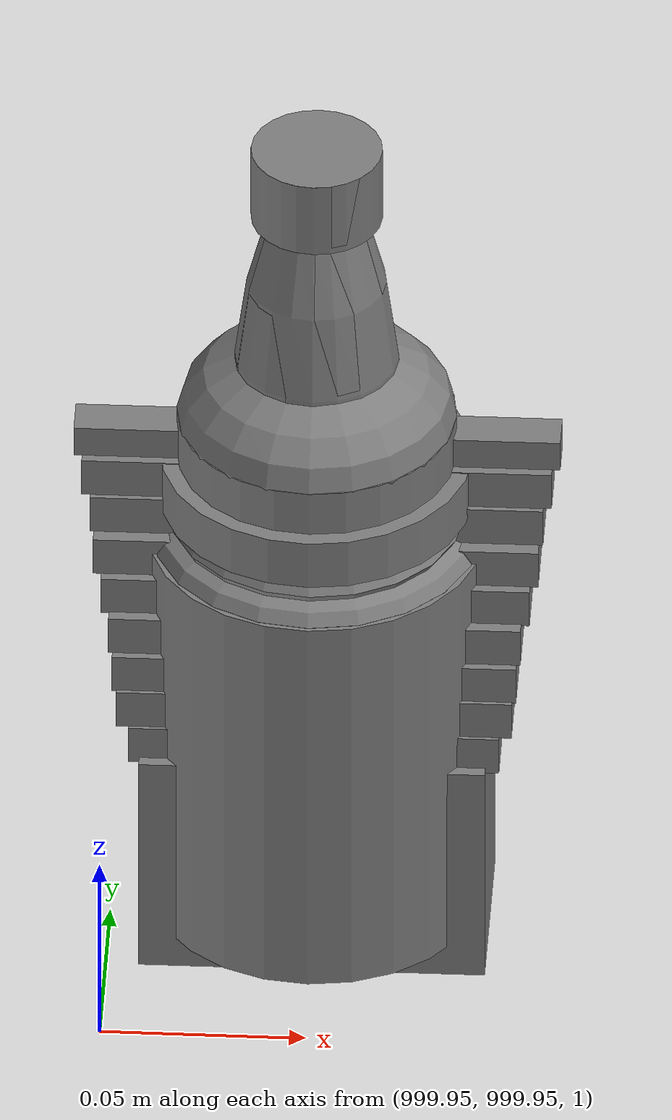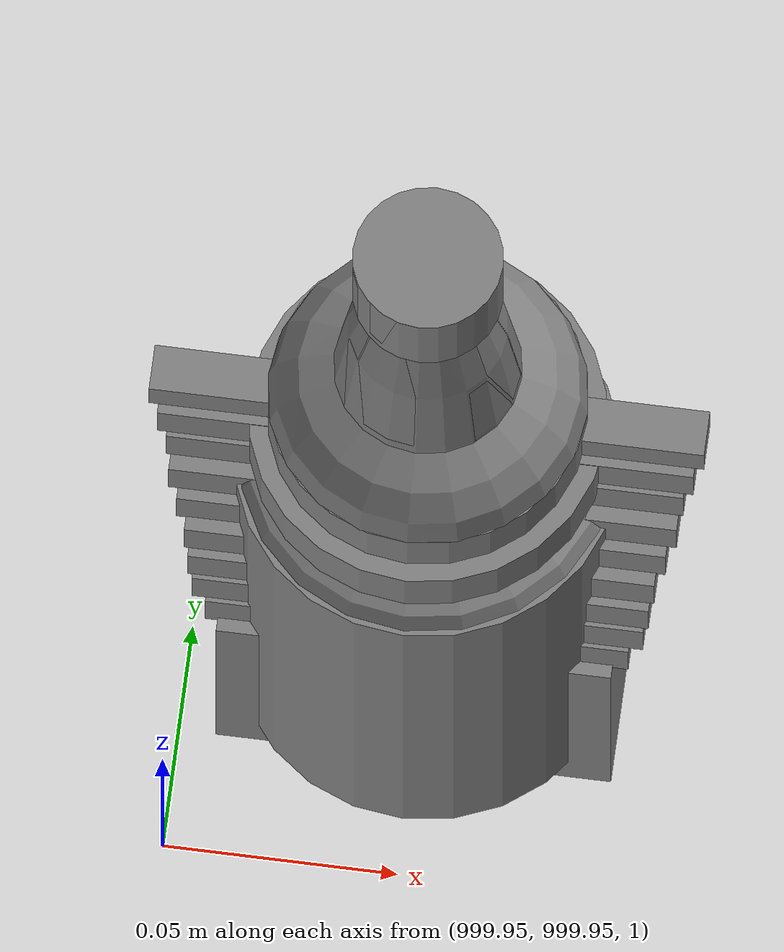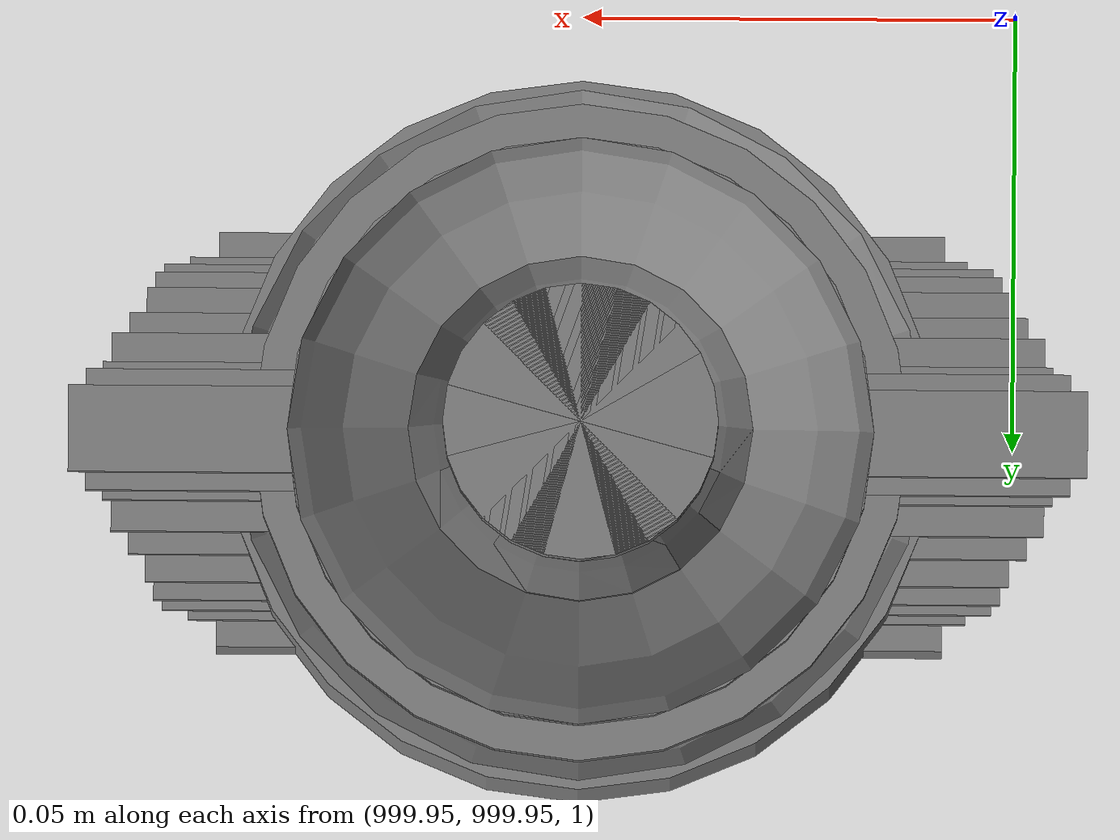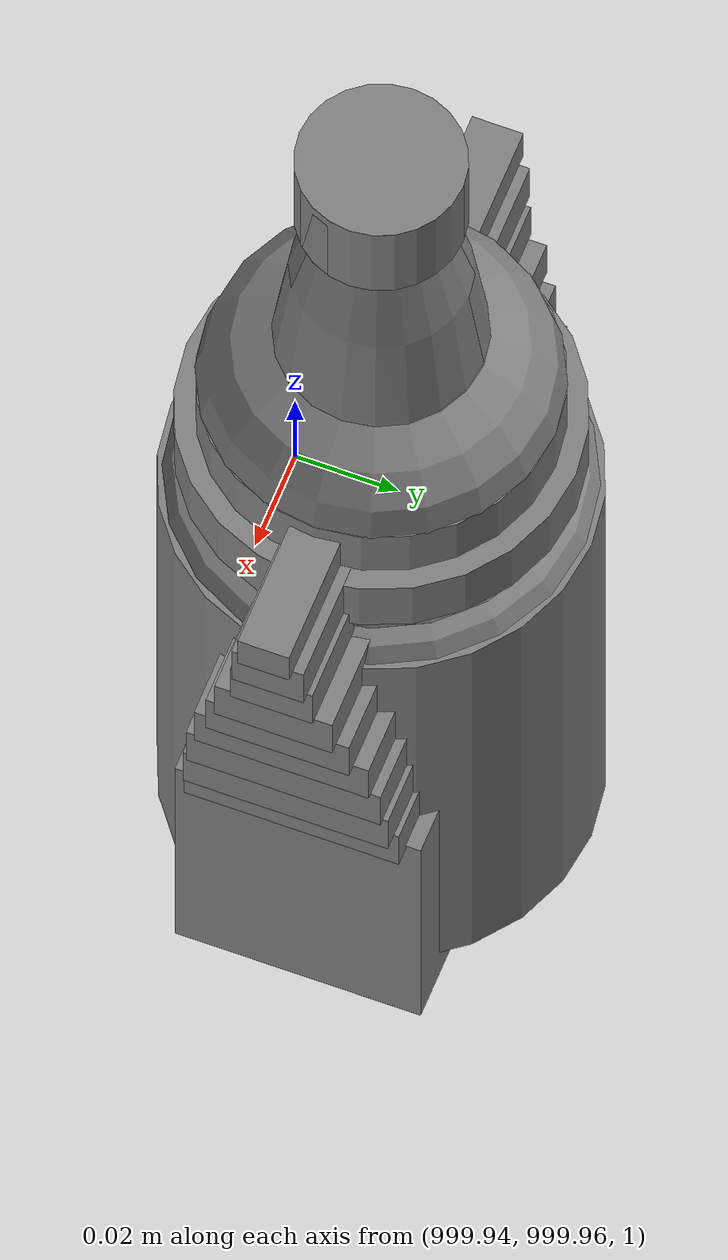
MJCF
<mujoco>
    <option gravity="0.000000000 0.000000000 -9.810000420" timestep="0.0166666" integrator="implicitfast" density="1.225" viscosity="1.8000001e-05" noslip_iterations="10" iterations="100" sdf_iterations="50">
        <flag multiccd="disable"/>
    </option>
    <size memory="1000M"/>
    <compiler coordinate="local"/>
    <worldbody>
        <light cutoff="30" pos="0 1 1" dir="0 -1 -2"/>
        <light cutoff="30" pos="0 -1 1" dir="0 1 -2"/>
        <body pos="0.000000000 0.000000000 0.000000000" euler="0.000000000 0.000000000 0.000000000" name="Interactive Objects_Interactive Objects"/>
        <body pos="-1.849815011 5.784532070 1.818724513" euler="31.105895996 3.970565557 -161.611358643" mocap="true" name="spotlight5_SpotLight"/>
        <body pos="1000.000000000 1000.000000000 1.000000000" euler="0.000000000 0.000000000 0.000000000" name="openloong_gripper_2f85_fix_base_usda_bottle_blue">
            <geom contype="1" conaffinity="1" density="1000" type="ellipsoid" material="" rgba="0.500000000 0.500000000 0.500000000 1.000000000" solimp="0.899999976 0.949999988 0.001000000" friction="1.000000000 0.005000000 0.000100000" solref="0.020000000 1.000000000" margin="0" condim="3" group="0" pos="0.000000000 0.000000000 0.118920922" quat="1.000000000 0.000000000 0.000000000 0.000000000" size="0.030999999 0.030999999 0.029999999" name="openloong_gripper_2f85_fix_base_usda_geom_80E26F03_EB0D_478F_AA0E_FD423E4F5653"/>
            <geom contype="1" conaffinity="1" density="1000" type="box" material="" rgba="0.500000000 0.500000000 0.500000000 1.000000000" solimp="0.899999976 0.949999988 0.001000000" friction="1.000000000 0.005000000 0.000100000" solref="0.020000000 1.000000000" margin="0" condim="3" group="0" pos="0.000000000 0.000000000 0.002164602" quat="1.000000000 0.000000000 0.000000000 0.000000000" size="0.020000000 0.020000000 0.003000000" name="openloong_gripper_2f85_fix_base_usda_geom_2F694829_90DB_4ACF_AAA6_07A93779B9AF"/>
            <geom contype="1" conaffinity="1" density="1000" type="cylinder" material="" rgba="0.500000000 0.500000000 0.500000000 1.000000000" solimp="0.899999976 0.949999988 0.001000000" friction="1.000000000 0.005000000 0.000100000" solref="0.020000000 1.000000000" margin="0" condim="3" group="0" pos="0.000000000 -0.000366211 0.060859680" quat="1.000000000 0.000000000 0.000000000 0.000000000" size="0.030999999 0.057999998 1.000000000" name="openloong_gripper_2f85_fix_base_usda_geom_976CC524_1E1C_4FB3_99DD_FF9FF9E9B4E8"/>
            <geom contype="1" conaffinity="1" density="1000" type="cylinder" material="" rgba="0.500000000 0.500000000 0.500000000 1.000000000" solimp="0.899999976 0.949999988 0.001000000" friction="1.000000000 0.005000000 0.000100000" solref="0.020000000 1.000000000" margin="0" condim="3" group="0" pos="0.000000000 0.000000000 0.220594406" quat="1.000000000 0.000000000 0.000000000 0.000000000" size="0.016000001 0.010000000 1.000000000" name="openloong_gripper_2f85_fix_base_usda_geom_8933D645_68A3_442A_B199_14CD5DFA399F"/>
            <geom contype="1" conaffinity="1" density="1000" type="ellipsoid" material="" rgba="0.500000000 0.500000000 0.500000000 1.000000000" solimp="0.899999976 0.949999988 0.001000000" friction="1.000000000 0.005000000 0.000100000" solref="0.020000000 1.000000000" margin="0" condim="3" group="0" pos="0.000000000 0.000000000 0.144259930" quat="1.000000000 0.000000000 0.000000000 0.000000000" size="0.021000000 0.021000000 0.079999998" name="openloong_gripper_2f85_fix_base_usda_geom_7F1192D6_FF1C_48C1_8AB5_34CFA426AD22"/>
            <freejoint name="openloong_gripper_2f85_fix_base_usda_bottle_blue_joint"/>
            <site size="0.005000000 0.005000000 0.005000000" rgba="0.500000000 0.500000000 0.500000000 1.000000000" pos="0.000000000 0.000000000 0.000000000" quat="0.999961913 0.008726535 0.000000000 0.000000000" group="0" type="sphere" name="openloong_gripper_2f85_fix_base_usda_bottle_bluesite"/>
        </body>
        <body pos="1000.000000000 1000.000000000 1.000000000" euler="0.000000000 0.000000000 0.000000000" name="openloong_gripper_2f85_fix_base_usda_bottle_red">
            <geom contype="1" conaffinity="1" density="1000" type="ellipsoid" material="" rgba="0.500000000 0.500000000 0.500000000 1.000000000" solimp="0.899999976 0.949999988 0.001000000" friction="1.000000000 0.005000000 0.000100000" solref="0.020000000 1.000000000" margin="0" condim="3" group="0" pos="0.000000000 0.000000000 0.144284487" quat="1.000000000 0.000000000 0.000000000 0.000000000" size="0.021000000 0.021000000 0.079999998" name="openloong_gripper_2f85_fix_base_usda_geom_3B15B583_0153_4989_B141_9F0D2C7DA303"/>
            <geom contype="1" conaffinity="1" density="1000" type="cylinder" material="" rgba="0.500000000 0.500000000 0.500000000 1.000000000" solimp="0.899999976 0.949999988 0.001000000" friction="1.000000000 0.005000000 0.000100000" solref="0.020000000 1.000000000" margin="0" condim="3" group="0" pos="0.000000000 0.000000000 0.220618963" quat="1.000000000 0.000000000 0.000000000 0.000000000" size="0.016000001 0.010000000 1.000000000" name="openloong_gripper_2f85_fix_base_usda_geom_392D7D3D_3BF2_49E3_81DE_F6458FBF9445"/>
            <geom contype="1" conaffinity="1" density="1000" type="ellipsoid" material="" rgba="0.500000000 0.500000000 0.500000000 1.000000000" solimp="0.899999976 0.949999988 0.001000000" friction="1.000000000 0.005000000 0.000100000" solref="0.020000000 1.000000000" margin="0" condim="3" group="0" pos="0.000000000 0.000000000 0.118945479" quat="1.000000000 0.000000000 0.000000000 0.000000000" size="0.030999999 0.030999999 0.029999999" name="openloong_gripper_2f85_fix_base_usda_geom_9C98747C_4915_4C89_9627_610FA3B9986A"/>
            <geom contype="1" conaffinity="1" density="1000" type="box" material="" rgba="0.500000000 0.500000000 0.500000000 1.000000000" solimp="0.899999976 0.949999988 0.001000000" friction="1.000000000 0.005000000 0.000100000" solref="0.020000000 1.000000000" margin="0" condim="3" group="0" pos="0.000000000 0.000000000 0.002189159" quat="1.000000000 0.000000000 0.000000000 0.000000000" size="0.020000000 0.020000000 0.003000000" name="openloong_gripper_2f85_fix_base_usda_geom_D10759FC_896A_45B9_8AC5_FB6F5741C310"/>
            <geom contype="1" conaffinity="1" density="1000" type="cylinder" material="" rgba="0.500000000 0.500000000 0.500000000 1.000000000" solimp="0.899999976 0.949999988 0.001000000" friction="1.000000000 0.005000000 0.000100000" solref="0.020000000 1.000000000" margin="0" condim="3" group="0" pos="0.000000000 -0.000366211 0.060884237" quat="1.000000000 0.000000000 0.000000000 0.000000000" size="0.030999999 0.057999998 1.000000000" name="openloong_gripper_2f85_fix_base_usda_geom_7EF87A5F_7C4D_4E80_BD2F_AA3AFFA92A0F"/>
            <freejoint name="openloong_gripper_2f85_fix_base_usda_bottle_red_joint"/>
            <site size="0.005000000 0.005000000 0.005000000" rgba="0.500000000 0.500000000 0.500000000 1.000000000" pos="0.000000000 0.000000000 0.000000000" quat="0.999961913 0.008726535 0.000000000 0.000000000" group="0" type="sphere" name="openloong_gripper_2f85_fix_base_usda_bottle_redsite"/>
        </body>
        <body pos="1000.000000000 1000.000000000 1.000000000" euler="0.000000000 0.000000000 0.000000000" name="openloong_gripper_2f85_fix_base_usda_salt">
            <geom contype="1" conaffinity="1" density="1000" type="box" material="" rgba="0.500000000 0.500000000 0.500000000 1.000000000" solimp="0.899999976 0.949999988 0.001000000" friction="1.000000000 0.005000000 0.000100000" solref="0.020000000 1.000000000" margin="0" condim="3" group="0" pos="0.000305176 0.000000000 0.084862232" quat="1.000000000 0.000000000 0.000000000 0.000000000" size="0.048999999 0.018999999 0.005000000" name="openloong_gripper_2f85_fix_base_usda_geom_ACEE30EE_8E6F_4B41_9010_643C9E54B225"/>
            <geom contype="1" conaffinity="1" density="1000" type="box" material="" rgba="0.500000000 0.500000000 0.500000000 1.000000000" solimp="0.899999976 0.949999988 0.001000000" friction="1.000000000 0.005000000 0.000100000" solref="0.020000000 1.000000000" margin="0" condim="3" group="0" pos="0.000305176 0.000000000 0.104564309" quat="1.000000000 0.000000000 0.000000000 0.000000000" size="0.052000001 0.014000000 0.005000000" name="openloong_gripper_2f85_fix_base_usda_geom_8201230C_37BF_409B_9069_BD8BF425A0F0"/>
            <geom contype="1" conaffinity="1" density="1000" type="box" material="" rgba="0.500000000 0.500000000 0.500000000 1.000000000" solimp="0.899999976 0.949999988 0.001000000" friction="1.000000000 0.005000000 0.000100000" solref="0.020000000 1.000000000" margin="0" condim="3" group="0" pos="0.000305176 0.000000000 0.114487171" quat="1.000000000 0.000000000 0.000000000 0.000000000" size="0.054000001 0.011500000 0.005000000" name="openloong_gripper_2f85_fix_base_usda_geom_ED4C3FB0_EF7A_47A6_BF54_244C66DD2DD9"/>
            <geom contype="1" conaffinity="1" density="1000" type="box" material="" rgba="0.500000000 0.500000000 0.500000000 1.000000000" solimp="0.899999976 0.949999988 0.001000000" friction="1.000000000 0.005000000 0.000100000" solref="0.020000000 1.000000000" margin="0" condim="3" group="0" pos="0.000305176 0.000000000 0.075103164" quat="1.000000000 0.000000000 0.000000000 0.000000000" size="0.048000000 0.020000000 0.005000000" name="openloong_gripper_2f85_fix_base_usda_geom_AB120CCB_D4F5_43BB_8C19_1844BAB309D7"/>
            <geom contype="1" conaffinity="1" density="1000" type="box" material="" rgba="0.500000000 0.500000000 0.500000000 1.000000000" solimp="0.899999976 0.949999988 0.001000000" friction="1.000000000 0.005000000 0.000100000" solref="0.020000000 1.000000000" margin="0" condim="3" group="0" pos="0.000305176 0.000000000 0.134892464" quat="1.000000000 0.000000000 0.000000000 0.000000000" size="0.057000000 0.007000000 0.005000000" name="openloong_gripper_2f85_fix_base_usda_geom_8991E0F7_9AE3_445F_8B90_FA69C0A0AF20"/>
            <geom contype="1" conaffinity="1" density="1000" type="box" material="" rgba="0.500000000 0.500000000 0.500000000 1.000000000" solimp="0.899999976 0.949999988 0.001000000" friction="1.000000000 0.005000000 0.000100000" solref="0.020000000 1.000000000" margin="0" condim="3" group="0" pos="0.000305176 0.000000000 0.094920278" quat="1.000000000 0.000000000 0.000000000 0.000000000" size="0.050000001 0.017000001 0.005000000" name="openloong_gripper_2f85_fix_base_usda_geom_FFF00A2A_3765_4104_86F1_65696F7172A8"/>
            <geom contype="1" conaffinity="1" density="1000" type="box" material="" rgba="0.500000000 0.500000000 0.500000000 1.000000000" solimp="0.899999976 0.949999988 0.001000000" friction="1.000000000 0.005000000 0.000100000" solref="0.020000000 1.000000000" margin="0" condim="3" group="0" pos="0.000305176 0.000000000 0.065204859" quat="1.000000000 0.000000000 0.000000000 0.000000000" size="0.045000002 0.021000000 0.005000000" name="openloong_gripper_2f85_fix_base_usda_geom_343A00A8_07AE_4228_A1CE_7B0AD81CD722"/>
            <geom contype="1" conaffinity="1" density="1000" type="box" material="" rgba="0.500000000 0.500000000 0.500000000 1.000000000" solimp="0.899999976 0.949999988 0.001000000" friction="1.000000000 0.005000000 0.000100000" solref="0.020000000 1.000000000" margin="0" condim="3" group="0" pos="0.000305176 0.000000000 0.144135714" quat="1.000000000 0.000000000 0.000000000 0.000000000" size="0.059000000 0.005000000 0.004000000" name="openloong_gripper_2f85_fix_base_usda_geom_0B0719ED_7515_450E_AD1B_6B828380492E"/>
            <geom contype="1" conaffinity="1" density="1000" type="box" material="" rgba="0.500000000 0.500000000 0.500000000 1.000000000" solimp="0.899999976 0.949999988 0.001000000" friction="1.000000000 0.005000000 0.000100000" solref="0.020000000 1.000000000" margin="0" condim="3" group="0" pos="0.000000000 0.000000000 0.031593561" quat="1.000000000 0.000000000 0.000000000 0.000000000" size="0.041999999 0.024000000 0.029999999" name="openloong_gripper_2f85_fix_base_usda_geom_E6A5B618_8A2C_4A58_9A47_1A608151ABE3"/>
            <geom contype="1" conaffinity="1" density="1000" type="box" material="" rgba="0.500000000 0.500000000 0.500000000 1.000000000" solimp="0.899999976 0.949999988 0.001000000" friction="1.000000000 0.005000000 0.000100000" solref="0.020000000 1.000000000" margin="0" condim="3" group="0" pos="0.000305176 0.000000000 0.124608755" quat="1.000000000 0.000000000 0.000000000 0.000000000" size="0.055000000 0.008000000 0.005000000" name="openloong_gripper_2f85_fix_base_usda_geom_7E686BA8_AA26_4C3F_BFA7_250C20434337"/>
            <freejoint name="openloong_gripper_2f85_fix_base_usda_salt_joint"/>
            <site size="0.005000000 0.005000000 0.005000000" rgba="0.500000000 0.500000000 0.500000000 1.000000000" pos="0.000000000 0.000000000 0.000000000" quat="1.000000000 0.000000000 0.000000000 0.000000000" group="0" type="sphere" name="openloong_gripper_2f85_fix_base_usda_saltsite"/>
        </body>
        <body pos="-2.309438705 6.655346870 1.842580914" euler="136.645675659 -45.824424744 51.109813690" mocap="true" name="spotlight2_SpotLight"/>
        <body pos="1000.000000000 1000.000000000 1.000000000" euler="0.000000000 0.000000000 0.000000000" name="openloong_gripper_2f85_fix_base_usda_can">
            <geom contype="1" conaffinity="1" density="1000" type="cylinder" material="" rgba="0.500000000 0.500000000 0.500000000 1.000000000" solimp="0.899999976 0.949999988 0.001000000" friction="1.000000000 0.005000000 0.000100000" solref="0.020000000 1.000000000" margin="0" condim="3" group="0" pos="0.000000000 0.000000000 0.079676986" quat="1.000000000 0.000000000 0.000000000 0.000000000" size="0.034000002 0.071999997 1.000000000" name="openloong_gripper_2f85_fix_base_usda_geom_A665EB31_D3C9_428F_A5E6_1006126F0460"/>
            <geom contype="1" conaffinity="1" density="1000" type="ellipsoid" material="" rgba="0.500000000 0.500000000 0.500000000 1.000000000" solimp="0.899999976 0.949999988 0.001000000" friction="1.000000000 0.005000000 0.000100000" solref="0.020000000 1.000000000" margin="0" condim="3" group="0" pos="0.000000000 0.000000000 0.151854277" quat="1.000000000 0.000000000 0.000000000 0.000000000" size="0.034000002 0.034000002 0.020000000" name="openloong_gripper_2f85_fix_base_usda_geom_62E91CF0_1BA7_45E8_A890_636B62DA1BD1"/>
            <geom contype="1" conaffinity="1" density="1000" type="box" material="" rgba="0.500000000 0.500000000 0.500000000 1.000000000" solimp="0.899999976 0.949999988 0.001000000" friction="1.000000000 0.005000000 0.000100000" solref="0.020000000 1.000000000" margin="0" condim="3" group="0" pos="0.000000000 0.000000000 0.004777670" quat="1.000000000 0.000000000 0.000000000 0.000000000" size="0.020000000 0.020000000 0.005000000" name="openloong_gripper_2f85_fix_base_usda_geom_DE8FAC25_1EA2_444F_8E3F_B7ECDC2C56F2"/>
            <freejoint name="openloong_gripper_2f85_fix_base_usda_can_joint"/>
            <site size="0.005000000 0.005000000 0.005000000" rgba="0.500000000 0.500000000 0.500000000 1.000000000" pos="0.000000000 0.000000000 0.000000000" quat="1.000000000 0.000000000 0.000000000 0.000000000" group="0" type="sphere" name="openloong_gripper_2f85_fix_base_usda_cansite"/>
        </body>
        <body pos="-2.300961733 6.433279514 1.724770308" euler="111.712699890 27.194370270 9.369074821" mocap="true" name="spotlight1_SpotLight"/>
        <body pos="1000.000000000 1000.000000000 1.000000000" euler="0.000000000 0.000000000 0.000000000" name="openloong_gripper_2f85_fix_base_usda_jar_01">
            <geom contype="1" conaffinity="1" density="1000" type="box" material="" rgba="0.500000000 0.500000000 0.500000000 1.000000000" solimp="0.899999976 0.949999988 0.001000000" friction="1.000000000 0.005000000 0.000100000" solref="0.020000000 1.000000000" margin="0" condim="3" group="0" pos="0.000000000 0.000000000 0.006158113" quat="1.000000000 0.000000000 0.000000000 0.000000000" size="0.020000000 0.020000000 0.005000000" name="openloong_gripper_2f85_fix_base_usda_geom_C9712D83_8554_42B8_9540_A81E2035C62F"/>
            <geom contype="1" conaffinity="1" density="1000" type="cylinder" material="" rgba="0.500000000 0.500000000 0.500000000 1.000000000" solimp="0.899999976 0.949999988 0.001000000" friction="1.000000000 0.005000000 0.000100000" solref="0.020000000 1.000000000" margin="0" condim="3" group="0" pos="0.000000000 0.000000000 0.062744498" quat="1.000000000 0.000000000 0.000000000 0.000000000" size="0.041000001 0.052999999 1.000000000" name="openloong_gripper_2f85_fix_base_usda_geom_83EFA900_7E4A_44AC_A35E_FAB694587BA5"/>
            <geom contype="1" conaffinity="1" density="1000" type="ellipsoid" material="" rgba="0.500000000 0.500000000 0.500000000 1.000000000" solimp="0.899999976 0.949999988 0.001000000" friction="1.000000000 0.005000000 0.000100000" solref="0.020000000 1.000000000" margin="0" condim="3" group="0" pos="0.000000000 0.000000000 0.122252703" quat="1.000000000 0.000000000 0.000000000 0.000000000" size="0.035999998 0.035999998 0.010000000" name="openloong_gripper_2f85_fix_base_usda_geom_7118D4A7_5F0B_46D3_B46D_32767F546F74"/>
            <geom contype="1" conaffinity="1" density="1000" type="cylinder" material="" rgba="0.500000000 0.500000000 0.500000000 1.000000000" solimp="0.899999976 0.949999988 0.001000000" friction="1.000000000 0.005000000 0.000100000" solref="0.020000000 1.000000000" margin="0" condim="3" group="0" pos="0.000000000 0.000000000 0.015747190" quat="1.000000000 0.000000000 0.000000000 0.000000000" size="0.035000000 0.010000000 1.000000000" name="openloong_gripper_2f85_fix_base_usda_geom_B316A789_F925_4EC1_94CE_B02D18E8F50E"/>
            <geom contype="1" conaffinity="1" density="1000" type="ellipsoid" material="" rgba="0.500000000 0.500000000 0.500000000 1.000000000" solimp="0.899999976 0.949999988 0.001000000" friction="1.000000000 0.005000000 0.000100000" solref="0.020000000 1.000000000" margin="0" condim="3" group="0" pos="0.000000000 0.000000000 0.115815401" quat="1.000000000 0.000000000 0.000000000 0.000000000" size="0.039999999 0.039999999 0.010000000" name="openloong_gripper_2f85_fix_base_usda_geom_FC79FF96_73FA_464A_AF9E_78C75756CF90"/>
            <geom contype="1" conaffinity="1" density="1000" type="cylinder" material="" rgba="0.500000000 0.500000000 0.500000000 1.000000000" solimp="0.899999976 0.949999988 0.001000000" friction="1.000000000 0.005000000 0.000100000" solref="0.020000000 1.000000000" margin="0" condim="3" group="0" pos="0.000000000 0.000000000 0.133183479" quat="1.000000000 0.000000000 0.000000000 0.000000000" size="0.037999999 0.006500000 1.000000000" name="openloong_gripper_2f85_fix_base_usda_geom_6FBB952D_BB38_4A23_A0DA_83082CFC2785"/>
            <freejoint name="openloong_gripper_2f85_fix_base_usda_jar_01_joint"/>
            <site size="0.005000000 0.005000000 0.005000000" rgba="0.500000000 0.500000000 0.500000000 1.000000000" pos="0.000000000 0.000000000 0.000000000" quat="1.000000000 0.000000000 0.000000000 0.000000000" group="0" type="sphere" name="openloong_gripper_2f85_fix_base_usda_jar_01site"/>
        </body>
        <body pos="0.000000000 0.000000000 0.000000000" euler="0.000000000 0.000000000 0.000000000" name=" Static Objects_ Static Objects">
            <geom contype="1" conaffinity="1" density="1000" type="box" material="" rgba="0.500000000 0.500000000 0.500000000 1.000000000" solimp="0.899999976 0.949999988 0.001000000" friction="1.000000000 0.005000000 0.000100000" solref="0.020000000 1.000000000" margin="0" condim="3" group="0" pos="-6.286010742 6.153595448 1.563861728" quat="0.707107067 0.000000000 0.000000000 0.707106471" size="0.529999971 3.134999990 0.025000000" name=" Static Objects_geom_EC8C64AB_1060_475D_8E80_E10024494A93"/>
            <geom contype="1" conaffinity="1" density="1000" type="box" material="" rgba="0.500000000 0.500000000 0.500000000 1.000000000" solimp="0.899999976 0.949999988 0.001000000" friction="1.000000000 0.005000000 0.000100000" solref="0.020000000 1.000000000" margin="0" condim="3" group="0" pos="-3.101639986 6.150595188 1.018643856" quat="1.000000000 0.000000000 0.000000000 0.000000000" size="0.050000001 0.579999983 1.019999981" name=" Static Objects_geom_0B694143_22F5_4BD9_816F_08D4EC798104"/>
            <geom contype="1" conaffinity="1" density="1000" type="box" material="" rgba="0.500000000 0.500000000 0.500000000 1.000000000" solimp="0.899999976 0.949999988 0.001000000" friction="1.000000000 0.005000000 0.000100000" solref="0.020000000 1.000000000" margin="0" condim="3" group="0" pos="-2.825197220 6.153595448 1.563861728" quat="0.707107067 0.000000000 0.000000000 0.707106471" size="0.550000012 0.239999995 0.025000000" name=" Static Objects_geom_B6BD3123_2766_41CD_A288_25DBBEC310AD"/>
            <geom contype="1" conaffinity="1" density="1000" type="box" material="" rgba="0.500000000 0.500000000 0.500000000 1.000000000" solimp="0.899999976 0.949999988 0.001000000" friction="1.000000000 0.005000000 0.000100000" solref="0.020000000 1.000000000" margin="0" condim="3" group="0" pos="-6.311686516 6.153595448 1.018643856" quat="0.707107067 0.000000000 0.000000000 0.707106471" size="0.050000001 3.150000095 1.019999981" name=" Static Objects_geom_729141CB_7541_4EA6_8265_C9191A1F9B5E"/>
            <geom contype="1" conaffinity="1" density="1000" type="box" material="" rgba="0.500000000 0.500000000 0.500000000 1.000000000" solimp="0.899999976 0.949999988 0.001000000" friction="1.000000000 0.005000000 0.000100000" solref="0.020000000 1.000000000" margin="0" condim="3" group="0" pos="-2.825197220 6.153595448 1.115278244" quat="0.707107067 0.000000000 0.000000000 0.707106471" size="0.550000012 0.239999995 0.025000000" name=" Static Objects_geom_8A40B7C1_0F36_434E_A1AA_EB96EFF6194D"/>
            <geom contype="1" conaffinity="1" density="1000" type="box" material="" rgba="0.500000000 0.500000000 0.500000000 1.000000000" solimp="0.899999976 0.949999988 0.001000000" friction="1.000000000 0.005000000 0.000100000" solref="0.020000000 1.000000000" margin="0" condim="3" group="0" pos="-6.293097973 6.153595448 1.114443064" quat="0.707107067 0.000000000 0.000000000 0.707106471" size="0.529999971 3.134999990 0.025000000" name=" Static Objects_geom_7A8B77EB_1807_4205_BB61_95CDBB63693A"/>
            <geom contype="1" conaffinity="1" density="1000" type="box" material="" rgba="0.500000000 0.500000000 0.500000000 1.000000000" solimp="0.899999976 0.949999988 0.001000000" friction="1.000000000 0.005000000 0.000100000" solref="0.020000000 1.000000000" margin="0" condim="3" group="0" pos="-2.825197220 6.153595448 0.629031777" quat="0.707107067 0.000000000 0.000000000 0.707106471" size="0.550000012 0.239999995 0.025000000" name=" Static Objects_geom_FFC5BD45_B329_4033_8F1A_FAAA13D1CAFC"/>
            <geom contype="1" conaffinity="1" density="1000" type="box" material="" rgba="0.500000000 0.500000000 0.500000000 1.000000000" solimp="0.899999976 0.949999988 0.001000000" friction="1.000000000 0.005000000 0.000100000" solref="0.020000000 1.000000000" margin="0" condim="3" group="0" pos="-6.286010742 6.153595448 0.096129179" quat="0.707107067 0.000000000 0.000000000 0.707106471" size="0.529999971 3.134999990 0.098999999" name=" Static Objects_geom_3B5A3640_18DD_4620_8B15_38D76DD133DF"/>
            <geom contype="1" conaffinity="1" density="1000" type="box" material="" rgba="0.500000000 0.500000000 0.500000000 1.000000000" solimp="0.899999976 0.949999988 0.001000000" friction="1.000000000 0.005000000 0.000100000" solref="0.020000000 1.000000000" margin="0" condim="3" group="0" pos="-2.825197220 6.153595448 0.097434282" quat="0.707107067 0.000000000 0.000000000 0.707106471" size="0.550000012 0.239999995 0.098999999" name=" Static Objects_geom_E137B2F4_AAF2_4536_A403_E62BC7B6DC3C"/>
            <geom contype="1" conaffinity="1" density="1000" type="box" material="" rgba="0.500000000 0.500000000 0.500000000 1.000000000" solimp="0.899999976 0.949999988 0.001000000" friction="1.000000000 0.005000000 0.000100000" solref="0.020000000 1.000000000" margin="0" condim="3" group="0" pos="-6.286010742 6.153595448 0.629031777" quat="0.707107067 0.000000000 0.000000000 0.707106471" size="0.529999971 3.134999990 0.025000000" name=" Static Objects_geom_22087145_48BC_4CF7_B908_8881E1CB1A2A"/>
            <geom contype="1" conaffinity="1" density="1000" type="box" material="" rgba="0.500000000 0.500000000 0.500000000 1.000000000" solimp="0.899999976 0.949999988 0.001000000" friction="1.000000000 0.005000000 0.000100000" solref="0.020000000 1.000000000" margin="0" condim="3" group="0" pos="-6.000000000 20.159999847 2.000000000" quat="1.000000000 0.000000000 0.000000000 0.000000000" size="6.079999924 0.070000000 2.000000000" name=" Static Objects_geom_3A79FAF8_AEB4_4E67_93CF_F18A99764156"/>
            <geom contype="1" conaffinity="1" density="1000" type="box" material="" rgba="0.500000000 0.500000000 0.500000000 1.000000000" solimp="0.899999976 0.949999988 0.001000000" friction="1.000000000 0.005000000 0.000100000" solref="0.020000000 1.000000000" margin="0" condim="3" group="0" pos="-6.000000000 0.035000000 2.000000000" quat="1.000000000 0.000000000 0.000000000 0.000000000" size="6.079999924 0.070000000 2.000000000" name=" Static Objects_geom_5F4E3E83_4938_4063_AC9A_50CB80988913"/>
            <geom contype="1" conaffinity="1" density="1000" type="box" material="" rgba="0.500000000 0.500000000 0.500000000 1.000000000" solimp="0.899999976 0.949999988 0.001000000" friction="1.000000000 0.005000000 0.000100000" solref="0.020000000 1.000000000" margin="0" condim="3" group="0" pos="0.000000000 10.000000000 2.000000000" quat="1.000000000 0.000000000 0.000000000 0.000000000" size="0.070000000 10.500000000 2.000000000" name=" Static Objects_geom_781DF943_75A1_438F_87E8_15EB2CF1A267"/>
            <geom contype="1" conaffinity="1" density="1000" type="box" material="" rgba="0.500000000 0.500000000 0.500000000 1.000000000" solimp="0.899999976 0.949999988 0.001000000" friction="1.000000000 0.005000000 0.000100000" solref="0.020000000 1.000000000" margin="0" condim="3" group="0" pos="-12.050000191 10.000000000 2.000000000" quat="1.000000000 0.000000000 0.000000000 0.000000000" size="0.070000000 10.500000000 2.000000000" name=" Static Objects_geom_E5CA2ED5_C706_4381_A420_05E07BE34745"/>
            <geom contype="1" conaffinity="1" density="1000" type="plane" material="" rgba="0.500000000 0.500000000 0.500000000 1.000000000" solimp="0.899999976 0.949999988 0.001000000" friction="1.000000000 0.005000000 0.000100000" solref="0.020000000 1.000000000" margin="0" condim="3" group="0" pos="-6.000000000 10.399999619 0.000000000" quat="1.000000000 0.000000000 0.000000000 0.000000000" size="6.050000191 10.800000191 0.010000000" name=" Static Objects_geom_C7CDC15F_E352_4DED_9232_2D2878D8B963"/>
            <geom contype="1" conaffinity="1" density="1000" type="box" material="" rgba="0.500000000 0.500000000 0.500000000 1.000000000" solimp="0.899999976 0.949999988 0.001000000" friction="1.000000000 0.005000000 0.000100000" solref="0.020000000 1.000000000" margin="0" condim="3" group="0" pos="-8.830721855 2.096410990 0.549305558" quat="1.000000000 0.000000000 0.000000000 0.000000000" size="0.280000001 0.430000007 0.550000012" name=" Static Objects_geom_32B568AE_0FD8_4CA7_AA8D_39C8B4F2C6C3"/>
            <geom contype="1" conaffinity="1" density="1000" type="box" material="" rgba="0.500000000 0.500000000 0.500000000 1.000000000" solimp="0.899999976 0.949999988 0.001000000" friction="1.000000000 0.005000000 0.000100000" solref="0.020000000 1.000000000" margin="0" condim="3" group="0" pos="-6.460197449 2.937205315 0.548931718" quat="1.000000000 0.000000000 0.000000000 0.000000000" size="2.650000095 0.430000007 0.550000012" name=" Static Objects_geom_8F6B864C_036E_44B4_AFCE_199D1D352888"/>
            <geom contype="1" conaffinity="1" density="1000" type="box" material="" rgba="0.500000000 0.500000000 0.500000000 1.000000000" solimp="0.899999976 0.949999988 0.001000000" friction="1.000000000 0.005000000 0.000100000" solref="0.020000000 1.000000000" margin="0" condim="3" group="0" pos="-4.240264893 1.327049494 0.549888909" quat="1.000000000 0.000000000 0.000000000 0.000000000" size="0.430000007 1.200000048 0.550000012" name=" Static Objects_geom_2741FA5A_2D7E_4425_8006_2B9D8ADC37E5"/>
            <geom contype="1" conaffinity="1" density="1000" type="box" material="" rgba="0.500000000 0.500000000 0.500000000 1.000000000" solimp="0.899999976 0.949999988 0.001000000" friction="1.000000000 0.005000000 0.000100000" solref="0.020000000 1.000000000" margin="0" condim="3" group="0" pos="-7.408766270 3.088089943 1.776644945" quat="0.928051054 0.000000000 0.000000000 0.372453064" size="0.050000001 0.100000001 0.050000001" name=" Static Objects_geom_378A4C4D_8542_4544_8645_DFEAB8A2CE35"/>
            <geom contype="1" conaffinity="1" density="1000" type="box" material="" rgba="0.500000000 0.500000000 0.500000000 1.000000000" solimp="0.899999976 0.949999988 0.001000000" friction="1.000000000 0.005000000 0.000100000" solref="0.020000000 1.000000000" margin="0" condim="3" group="0" pos="-7.437745571 3.067511320 1.289965630" quat="1.000000000 0.000000000 0.000000000 0.000000000" size="0.029999999 0.020000000 0.020000000" name=" Static Objects_geom_A6E19F4F_E751_4834_AE45_ED1CC50ADF5A"/>
            <geom contype="1" conaffinity="1" density="1000" type="box" material="" rgba="0.500000000 0.500000000 0.500000000 1.000000000" solimp="0.899999976 0.949999988 0.001000000" friction="1.000000000 0.005000000 0.000100000" solref="0.020000000 1.000000000" margin="0" condim="3" group="0" pos="-7.719123363 2.867671013 1.173410416" quat="1.000000000 0.000000000 0.000000000 0.000000000" size="0.250000000 0.250000000 0.079999998" name=" Static Objects_geom_4328178E_4CC8_4BC9_92E8_43A5703B943E"/>
            <geom contype="1" conaffinity="1" density="1000" type="box" material="" rgba="0.500000000 0.500000000 0.500000000 1.000000000" solimp="0.899999976 0.949999988 0.001000000" friction="1.000000000 0.005000000 0.000100000" solref="0.020000000 1.000000000" margin="0" condim="3" group="0" pos="-7.719123363 2.958004713 1.530241251" quat="1.000000000 0.000000000 0.000000000 0.000000000" size="0.250000000 0.159999996 0.280000001" name=" Static Objects_geom_D9089523_2A2D_4B55_9298_0376447E4582"/>
            <geom contype="1" conaffinity="1" density="1000" type="cylinder" material="" rgba="0.500000000 0.500000000 0.500000000 1.000000000" solimp="0.899999976 0.949999988 0.001000000" friction="1.000000000 0.005000000 0.000100000" solref="0.020000000 1.000000000" margin="0" condim="3" group="0" pos="-7.427312374 3.069516420 1.502544641" quat="0.928051054 0.000000000 0.000000000 0.372453064" size="0.015000000 0.230000004 0.100000001" name=" Static Objects_geom_1F924B37_AC56_4132_A77D_74C37280D5B7"/>
            <geom contype="1" conaffinity="1" density="1000" type="box" material="" rgba="0.500000000 0.500000000 0.500000000 1.000000000" solimp="0.899999976 0.949999988 0.001000000" friction="1.000000000 0.005000000 0.000100000" solref="0.020000000 1.000000000" margin="0" condim="3" group="0" pos="-9.058088303 6.434794426 1.209077358" quat="1.000000000 0.000000000 0.000000000 0.000000000" size="0.250000000 0.100000001 0.070000000" name=" Static Objects_geom_47514FBE_2A58_4532_BD3F_29AF54EA3235"/>
            <geom contype="1" conaffinity="1" density="1000" type="box" material="" rgba="0.500000000 0.500000000 0.500000000 1.000000000" solimp="0.899999976 0.949999988 0.001000000" friction="1.000000000 0.005000000 0.000100000" solref="0.020000000 1.000000000" margin="0" condim="3" group="0" pos="-5.611940861 6.318420410 0.350975692" quat="1.000000000 0.000000000 0.000000000 0.000000000" size="0.699999988 0.100000001 0.150000006" name=" Static Objects_geom_889F2D49_9B73_4DB7_85B6_4AAA188396BF"/>
            <geom contype="1" conaffinity="1" density="1000" type="box" material="" rgba="0.500000000 0.500000000 0.500000000 1.000000000" solimp="0.899999976 0.949999988 0.001000000" friction="1.000000000 0.005000000 0.000100000" solref="0.020000000 1.000000000" margin="0" condim="3" group="0" pos="-9.237723351 6.464855671 1.209077358" quat="1.000000000 0.000000000 0.000000000 0.000000000" size="0.100000001 0.100000001 0.070000000" name=" Static Objects_geom_129B529F_DB43_4C9A_900C_BD3CCFEFEB49"/>
            <geom contype="1" conaffinity="1" density="1000" type="box" material="" rgba="0.500000000 0.500000000 0.500000000 1.000000000" solimp="0.899999976 0.949999988 0.001000000" friction="1.000000000 0.005000000 0.000100000" solref="0.020000000 1.000000000" margin="0" condim="3" group="0" pos="-6.300771236 6.459744930 1.744376063" quat="1.000000000 0.000000000 0.000000000 0.000000000" size="3.000000000 0.200000003 0.150000006" name=" Static Objects_geom_1EBD7BAC_B992_4935_BB15_5464282C3B54"/>
            <geom contype="1" conaffinity="1" density="1000" type="box" material="" rgba="0.500000000 0.500000000 0.500000000 1.000000000" solimp="0.899999976 0.949999988 0.001000000" friction="1.000000000 0.005000000 0.000100000" solref="0.020000000 1.000000000" margin="0" condim="3" group="0" pos="-7.373087406 6.458900928 1.214329123" quat="1.000000000 0.000000000 0.000000000 0.000000000" size="0.250000000 0.200000003 0.075000003" name=" Static Objects_geom_E37FF06B_575D_47D9_AC11_9D3E4F8F5843"/>
            <geom contype="1" conaffinity="1" density="1000" type="box" material="" rgba="0.500000000 0.500000000 0.500000000 1.000000000" solimp="0.899999976 0.949999988 0.001000000" friction="1.000000000 0.005000000 0.000100000" solref="0.020000000 1.000000000" margin="0" condim="3" group="0" pos="-4.035642624 6.459744930 0.352518857" quat="1.000000000 0.000000000 0.000000000 0.000000000" size="0.800000012 0.200000003 0.150000006" name=" Static Objects_geom_F515FAA6_0486_4B1E_B3E9_997657591311"/>
            <geom contype="1" conaffinity="1" density="1000" type="box" material="" rgba="0.500000000 0.500000000 0.500000000 1.000000000" solimp="0.899999976 0.949999988 0.001000000" friction="1.000000000 0.005000000 0.000100000" solref="0.020000000 1.000000000" margin="0" condim="3" group="0" pos="-3.907610416 6.318625927 0.800981164" quat="1.000000000 0.000000000 0.000000000 0.000000000" size="0.500000000 0.100000001 0.150000006" name=" Static Objects_geom_4DDA494A_75EC_416D_8BA1_27AC2777CAF7"/>
            <geom contype="1" conaffinity="1" density="1000" type="box" material="" rgba="0.500000000 0.500000000 0.500000000 1.000000000" solimp="0.899999976 0.949999988 0.001000000" friction="1.000000000 0.005000000 0.000100000" solref="0.020000000 1.000000000" margin="0" condim="3" group="0" pos="-6.098561764 6.327973843 1.292199373" quat="1.000000000 0.000000000 0.000000000 0.000000000" size="0.500000000 0.100000001 0.150000006" name=" Static Objects_geom_943025FB_B07F_43FB_9A78_7D25994D7710"/>
            <geom contype="1" conaffinity="1" density="1000" type="box" material="" rgba="0.500000000 0.500000000 0.500000000 1.000000000" solimp="0.899999976 0.949999988 0.001000000" friction="1.000000000 0.005000000 0.000100000" solref="0.020000000 1.000000000" margin="0" condim="3" group="0" pos="-7.886891365 6.459744930 0.352518857" quat="1.000000000 0.000000000 0.000000000 0.000000000" size="1.500000000 0.200000003 0.150000006" name=" Static Objects_geom_923C53E3_7E84_4830_BEFF_4BCF21E441C5"/>
            <geom contype="1" conaffinity="1" density="1000" type="box" material="" rgba="0.500000000 0.500000000 0.500000000 1.000000000" solimp="0.899999976 0.949999988 0.001000000" friction="1.000000000 0.005000000 0.000100000" solref="0.020000000 1.000000000" margin="0" condim="3" group="0" pos="-6.824534416 6.447464466 1.212718010" quat="1.000000000 0.000000000 0.000000000 0.000000000" size="0.100000001 0.100000001 0.075000003" name=" Static Objects_geom_C7525F21_3941_4F94_9D76_D1203F3E684D"/>
            <geom contype="1" conaffinity="1" density="1000" type="box" material="" rgba="0.500000000 0.500000000 0.500000000 1.000000000" solimp="0.899999976 0.949999988 0.001000000" friction="1.000000000 0.005000000 0.000100000" solref="0.020000000 1.000000000" margin="0" condim="3" group="0" pos="-4.407354832 6.459744930 1.292199373" quat="1.000000000 0.000000000 0.000000000 0.000000000" size="1.240000010 0.200000003 0.150000006" name=" Static Objects_geom_1F6F3882_86B4_4DAA_9A00_30B8AE51CB12"/>
            <geom contype="1" conaffinity="1" density="1000" type="box" material="" rgba="0.500000000 0.500000000 0.500000000 1.000000000" solimp="0.899999976 0.949999988 0.001000000" friction="1.000000000 0.005000000 0.000100000" solref="0.020000000 1.000000000" margin="0" condim="3" group="0" pos="-6.751636982 6.459744930 0.800981164" quat="1.000000000 0.000000000 0.000000000 0.000000000" size="2.200000048 0.200000003 0.150000006" name=" Static Objects_geom_A2274339_47AD_4196_8D07_0074228D55B2"/>
            <geom contype="1" conaffinity="1" density="1000" type="box" material="" rgba="0.500000000 0.500000000 0.500000000 1.000000000" solimp="0.899999976 0.949999988 0.001000000" friction="1.000000000 0.005000000 0.000100000" solref="0.020000000 1.000000000" margin="0" condim="3" group="0" pos="-6.924745083 6.362090111 1.214329123" quat="1.000000000 0.000000000 0.000000000 0.000000000" size="0.200000003 0.100000001 0.075000003" name=" Static Objects_geom_E3A5676D_05D4_40DA_A5AC_D5658DAD9BB5"/>
            <geom contype="1" conaffinity="1" density="1000" type="box" material="" rgba="0.500000000 0.500000000 0.500000000 1.000000000" solimp="0.899999976 0.949999988 0.001000000" friction="1.000000000 0.005000000 0.000100000" solref="0.020000000 1.000000000" margin="0" condim="3" group="0" pos="-8.844120979 6.464855671 1.209077358" quat="1.000000000 0.000000000 0.000000000 0.000000000" size="0.100000001 0.100000001 0.070000000" name=" Static Objects_geom_272982A0_5AB3_474B_B7D6_C9A25A1B6F97"/>
            <geom contype="1" conaffinity="1" density="1000" type="box" material="" rgba="0.500000000 0.500000000 0.500000000 1.000000000" solimp="0.899999976 0.949999988 0.001000000" friction="1.000000000 0.005000000 0.000100000" solref="0.020000000 1.000000000" margin="0" condim="3" group="0" pos="-3.157672644 6.136868477 1.348373055" quat="1.000000000 0.000000000 0.000000000 0.000000000" size="0.200000003 0.519999981 0.300000012" name=" Static Objects_geom_9F8CE6F3_D758_4EBB_BDDE_88895D131C9C"/>
        </body>
        <body pos="-6.332345009 2.779978037 1.034067392" euler="0.000000000 0.000000000 0.000000000" name="openloong_gripper_2f85_fix_base_usda_basket">
            <geom contype="1" conaffinity="1" density="100000" type="box" material="" rgba="0.500000000 0.500000000 0.500000000 1.000000000" solimp="0.899999976 0.949999988 0.001000000" friction="1.000000000 0.899999976 0.000100000" solref="0.020000000 1.000000000" margin="0" condim="3" group="0" pos="-0.039724827 -0.188568115 0.167089701" quat="0.997537494 0.070135131 0.000000000 0.000000000" size="0.150000006 0.006000000 0.108000003" name="openloong_gripper_2f85_fix_base_usda_geom_26ADBDFC_8A93_4E8A_B0ED_40AAFF6B23C7"/>
            <geom contype="1" conaffinity="1" density="100000" type="box" material="" rgba="0.500000000 0.500000000 0.500000000 1.000000000" solimp="0.899999976 0.949999988 0.001000000" friction="1.000000000 0.899999976 0.000100000" solref="0.020000000 1.000000000" margin="0" condim="3" group="0" pos="0.094372749 0.000000000 0.168361664" quat="0.706172049 0.036353335 0.036353379 0.706171215" size="0.200000003 0.006000000 0.108000003" name="openloong_gripper_2f85_fix_base_usda_geom_1531EA1A_8CD2_4D06_A44A_69573DBD4518"/>
            <geom contype="1" conaffinity="1" density="100000" type="box" material="" rgba="0.500000000 0.500000000 0.500000000 1.000000000" solimp="0.899999976 0.949999988 0.001000000" friction="1.000000000 0.899999976 0.000100000" solref="0.020000000 1.000000000" margin="0" condim="3" group="0" pos="-0.039724827 0.000000000 0.068126202" quat="1.000000000 0.000000000 0.000000000 0.000000000" size="0.129999995 0.174999997 0.006000000" name="openloong_gripper_2f85_fix_base_usda_geom_12EE5970_5399_4D96_9569_55CA6FB38B2B"/>
            <geom contype="1" conaffinity="1" density="100000" type="box" material="" rgba="0.500000000 0.500000000 0.500000000 1.000000000" solimp="0.899999976 0.949999988 0.001000000" friction="1.000000000 0.899999976 0.000100000" solref="0.020000000 1.000000000" margin="0" condim="3" group="0" pos="-0.039724827 0.188377380 0.167089701" quat="0.997489929 -0.070808925 0.000000000 0.000000000" size="0.150000006 0.006000000 0.108000003" name="openloong_gripper_2f85_fix_base_usda_geom_9251E13F_0642_42DB_8D0C_7955B5128F20"/>
            <geom contype="1" conaffinity="1" density="100000" type="box" material="" rgba="0.500000000 0.500000000 0.500000000 1.000000000" solimp="0.899999976 0.949999988 0.001000000" friction="1.000000000 0.899999976 0.000100000" solref="0.020000000 1.000000000" margin="0" condim="3" group="0" pos="-0.172339439 0.000000000 0.168361664" quat="0.706172407 -0.036353018 -0.036353093 0.706170976" size="0.200000003 0.006000000 0.108000003" name="openloong_gripper_2f85_fix_base_usda_geom_2B4B5CF7_F3FD_4894_8678_A9C3AD3ABDA7"/>
            <freejoint name="openloong_gripper_2f85_fix_base_usda_basket_joint"/>
            <site size="0.005000000 0.005000000 0.005000000" rgba="0.500000000 0.500000000 0.500000000 1.000000000" pos="0.000000000 0.000000000 0.000000000" quat="1.000000000 0.000000000 0.000000000 0.000000000" group="0" type="sphere" name="openloong_gripper_2f85_fix_base_usda_basketsite"/>
        </body>
        <body pos="-3.510578632 3.403555870 -0.000000100" euler="0.000000000 0.000000000 40.200675964" name="openloong_gripper_2f85_fix_base_usda_PZ">
            <geom contype="1" conaffinity="1" density="1000" type="box" material="" rgba="0.500000000 0.500000000 0.500000000 1.000000000" solimp="0.899999976 0.949999988 0.001000000" friction="1.000000000 0.005000000 0.000100000" solref="0.020000000 1.000000000" margin="0" condim="3" group="0" pos="-0.047453165 0.056484699 0.373715430" quat="0.934750080 0.077914521 0.028795123 0.345459938" size="0.180000007 0.010000000 0.379999995" name="openloong_gripper_2f85_fix_base_usda_geom_004840E6_6450_40B2_AE56_0A373E4833FC"/>
            <geom contype="1" conaffinity="1" density="1000" type="box" material="" rgba="0.500000000 0.500000000 0.500000000 1.000000000" solimp="0.899999976 0.949999988 0.001000000" friction="1.000000000 0.005000000 0.000100000" solref="0.020000000 1.000000000" margin="0" condim="3" group="0" pos="0.047452450 -0.054376602 0.374072611" quat="0.934387863 -0.082143910 -0.030358355 0.345326364" size="0.180000007 0.010000000 0.379999995" name="openloong_gripper_2f85_fix_base_usda_geom_2FAD0952_BDB9_42FB_AC25_EB6C511FC67F"/>
            <freejoint name="openloong_gripper_2f85_fix_base_usda_PZ"/>
        </body>
        <body pos="-7.168000221 2.823999882 1.227496982" euler="-0.283413976 0.056829724 -0.133293271" name="openloong_gripper_2f85_fix_base_usda_Pos">
            <geom contype="1" conaffinity="1" density="1000" type="box" material="" rgba="0.500000000 0.500000000 0.500000000 1.000000000" solimp="0.899999976 0.949999988 0.001000000" friction="1.000000000 0.005000000 0.000100000" solref="0.020000000 1.000000000" margin="0" condim="3" group="0" pos="-0.002278805 0.074524641 -0.004134059" quat="0.315989345 0.948763072 -0.000000000 0.000000000" size="0.059999999 0.013000000 0.035000000" name="openloong_gripper_2f85_fix_base_usda_geom_48F28A9B_5C41_4615_8583_A6C1B34B44B1"/>
            <geom contype="1" conaffinity="1" density="1000" type="box" material="" rgba="0.500000000 0.500000000 0.500000000 1.000000000" solimp="0.899999976 0.949999988 0.001000000" friction="1.000000000 0.005000000 0.000100000" solref="0.020000000 1.000000000" margin="0" condim="3" group="0" pos="-0.002278805 0.078031301 0.008128285" quat="0.990447521 -0.137893379 -0.000000000 -0.000000000" size="0.059999999 0.010000000 0.035000000" name="openloong_gripper_2f85_fix_base_usda_geom_4D25113B_940C_49CF_B42C_196B8B81E265"/>
            <geom contype="1" conaffinity="1" density="1000" type="box" material="" rgba="0.500000000 0.500000000 0.500000000 1.000000000" solimp="0.899999976 0.949999988 0.001000000" friction="1.000000000 0.005000000 0.000100000" solref="0.020000000 1.000000000" margin="0" condim="3" group="0" pos="-0.002278805 0.080785275 -0.002596974" quat="0.287325472 -0.957833409 0.000000000 -0.000000000" size="0.059999999 0.013000000 0.035000000" name="openloong_gripper_2f85_fix_base_usda_geom_723E7628_F4A0_4183_8D07_753E28A3AE43"/>
            <geom contype="1" conaffinity="1" density="1000" type="box" material="" rgba="0.500000000 0.500000000 0.500000000 1.000000000" solimp="0.899999976 0.949999988 0.001000000" friction="1.000000000 0.005000000 0.000100000" solref="0.020000000 1.000000000" margin="0" condim="3" group="0" pos="-0.002278805 -0.098804474 -0.020146966" quat="0.988851666 0.148906454 0.000000000 -0.000000000" size="0.059999999 0.022000000 0.020000000" name="openloong_gripper_2f85_fix_base_usda_geom_9D8FED7D_C92F_4178_84FF_6929999DE7C5"/>
            <geom contype="1" conaffinity="1" density="1000" type="box" material="" rgba="0.500000000 0.500000000 0.500000000 1.000000000" solimp="0.899999976 0.949999988 0.001000000" friction="1.000000000 0.005000000 0.000100000" solref="0.020000000 1.000000000" margin="0" condim="3" group="0" pos="-0.002279282 0.019920111 0.012102962" quat="0.995421767 0.095583342 -0.000000000 -0.000000000" size="0.059999999 0.025000000 0.026000001" name="openloong_gripper_2f85_fix_base_usda_geom_DA8F4564_497B_4A5E_AC44_E1BCA9B81E01"/>
            <geom contype="1" conaffinity="1" density="1000" type="box" material="" rgba="0.500000000 0.500000000 0.500000000 1.000000000" solimp="0.899999976 0.949999988 0.001000000" friction="1.000000000 0.005000000 0.000100000" solref="0.020000000 1.000000000" margin="0" condim="3" group="0" pos="-0.002279282 0.005734444 -0.014276862" quat="0.999571741 -0.029275302 -0.000000000 -0.000000000" size="0.059999999 0.050000001 0.010000000" name="openloong_gripper_2f85_fix_base_usda_geom_FC8338FB_07FC_4DC4_81CD_37B9CE24D791"/>
            <geom contype="1" conaffinity="1" density="1000" type="box" material="" rgba="0.500000000 0.500000000 0.500000000 1.000000000" solimp="0.899999976 0.949999988 0.001000000" friction="1.000000000 0.005000000 0.000100000" solref="0.020000000 1.000000000" margin="0" condim="3" group="0" pos="-0.002278805 0.079460382 0.007771969" quat="0.922590554 -0.385781586 0.000000000 -0.000000000" size="0.059999999 0.010000000 0.035000000" name="openloong_gripper_2f85_fix_base_usda_geom_F4C500BE_8AC3_4CF1_A0EF_EB8D227D830F"/>
            <geom contype="1" conaffinity="1" density="1000" type="box" material="" rgba="0.500000000 0.500000000 0.500000000 1.000000000" solimp="0.899999976 0.949999988 0.001000000" friction="1.000000000 0.005000000 0.000100000" solref="0.020000000 1.000000000" margin="0" condim="3" group="0" pos="-0.002279282 0.081384182 -0.001320124" quat="0.590483785 -0.807049930 0.000000000 -0.000000000" size="0.059999999 0.013000000 0.035000000" name="openloong_gripper_2f85_fix_base_usda_geom_41BF4706_D8A1_450B_826F_8E82E648A6FF"/>
            <geom contype="1" conaffinity="1" density="1000" type="box" material="" rgba="0.500000000 0.500000000 0.500000000 1.000000000" solimp="0.899999976 0.949999988 0.001000000" friction="1.000000000 0.005000000 0.000100000" solref="0.020000000 1.000000000" margin="0" condim="3" group="0" pos="-0.002278805 -0.059297800 -0.007972836" quat="0.988851666 0.148906454 0.000000000 -0.000000000" size="0.059999999 0.020000000 0.022000000" name="openloong_gripper_2f85_fix_base_usda_geom_0734A7EC_0308_48A7_B49E_F582B8BE8000"/>
            <geom contype="1" conaffinity="1" density="1000" type="box" material="" rgba="0.500000000 0.500000000 0.500000000 1.000000000" solimp="0.899999976 0.949999988 0.001000000" friction="1.000000000 0.005000000 0.000100000" solref="0.020000000 1.000000000" margin="0" condim="3" group="0" pos="-0.002278805 0.076618671 -0.004656792" quat="0.004634961 0.999989629 -0.000000000 0.000000000" size="0.059999999 0.013000000 0.035000000" name="openloong_gripper_2f85_fix_base_usda_geom_DAAEEADA_1A30_493C_8D04_40D7FFB91A98"/>
            <geom contype="1" conaffinity="1" density="1000" type="box" material="" rgba="0.500000000 0.500000000 0.500000000 1.000000000" solimp="0.899999976 0.949999988 0.001000000" friction="1.000000000 0.005000000 0.000100000" solref="0.020000000 1.000000000" margin="0" condim="3" group="0" pos="-0.002279282 -0.021952629 0.002960086" quat="0.991270423 0.131847665 -0.000000000 0.000000000" size="0.059999999 0.020000000 0.024000000" name="openloong_gripper_2f85_fix_base_usda_geom_37E1EF16_896C_4302_A987_0F5402CDC18E"/>
            <geom contype="1" conaffinity="1" density="1000" type="box" material="" rgba="0.500000000 0.500000000 0.500000000 1.000000000" solimp="0.899999976 0.949999988 0.001000000" friction="1.000000000 0.005000000 0.000100000" solref="0.020000000 1.000000000" margin="0" condim="3" group="0" pos="-0.002278805 0.081418991 0.002587914" quat="0.803492308 -0.595315695 0.000000000 -0.000000000" size="0.059999999 0.013000000 0.035000000" name="openloong_gripper_2f85_fix_base_usda_geom_9E0130E6_1A61_477E_B005_A70B4C9B8514"/>
            <geom contype="1" conaffinity="1" density="1000" type="box" material="" rgba="0.500000000 0.500000000 0.500000000 1.000000000" solimp="0.899999976 0.949999988 0.001000000" friction="1.000000000 0.005000000 0.000100000" solref="0.020000000 1.000000000" margin="0" condim="3" group="0" pos="-0.002278805 0.061115503 0.008545756" quat="0.999326169 0.036714450 0.000000000 -0.000000000" size="0.059999999 0.020000000 0.035000000" name="openloong_gripper_2f85_fix_base_usda_geom_05B29EAA_1DD5_4C3E_93E1_4522C4444D58"/>
            <freejoint name="openloong_gripper_2f85_fix_base_usda_pos_scan"/>
        </body>
        <body pos="-2.436573029 6.404376507 0.137849092" euler="0.000000000 0.000000000 0.000000000" name="openloong_gripper_2f85_fix_base_usda_shoppingtrolley_01">
            <geom contype="1" conaffinity="1" density="1000" type="box" material="" rgba="0.500000000 0.500000000 0.500000000 1.000000000" solimp="0.899999976 0.949999988 0.001000000" friction="1.000000000 0.005000000 0.000100000" solref="0.020000000 1.000000000" margin="0" condim="3" group="0" pos="-0.107458733 0.238907143 0.911498845" quat="0.634576976 0.622505128 -0.330067992 -0.317575932" size="0.017999999 0.022499999 0.035999998" name="openloong_gripper_2f85_fix_base_usda_geom_5AC6F07A_7BB7_4458_88C5_4D05DBE4A9C6"/>
            <geom contype="1" conaffinity="1" density="1000" type="box" material="" rgba="0.500000000 0.500000000 0.500000000 1.000000000" solimp="0.899999976 0.949999988 0.001000000" friction="1.000000000 0.005000000 0.000100000" solref="0.020000000 1.000000000" margin="0" condim="3" group="0" pos="-0.126757339 -0.182533979 0.598989725" quat="0.996607184 0.055331606 -0.059003651 -0.015205891" size="0.013499999 0.287999988 0.053999998" name="openloong_gripper_2f85_fix_base_usda_geom_D15173AC_C66E_4465_8587_B454DBB5F368"/>
            <geom contype="1" conaffinity="1" density="1000" type="box" material="" rgba="0.500000000 0.500000000 0.500000000 1.000000000" solimp="0.899999976 0.949999988 0.001000000" friction="1.000000000 0.005000000 0.000100000" solref="0.020000000 1.000000000" margin="0" condim="3" group="0" pos="-0.005004787 0.248085022 0.912686050" quat="1.000000000 0.000000000 0.000000000 0.000000000" size="0.107999995 0.022499999 0.022499999" name="openloong_gripper_2f85_fix_base_usda_geom_53AC64E2_8C18_427F_AEAB_8FD933B3D2E5"/>
            <geom contype="1" conaffinity="1" density="1000" type="box" material="" rgba="0.500000000 0.500000000 0.500000000 1.000000000" solimp="0.899999976 0.949999988 0.001000000" friction="1.000000000 0.005000000 0.000100000" solref="0.020000000 1.000000000" margin="0" condim="3" group="0" pos="-0.169898406 -0.043119621 0.915120542" quat="0.687021017 0.726584017 -0.005590606 -0.006832919" size="0.017999999 0.022499999 0.089999996" name="openloong_gripper_2f85_fix_base_usda_geom_EF4355E6_A2DE_452C_9E9F_1121FD202089"/>
            <geom contype="1" conaffinity="1" density="1000" type="box" material="" rgba="0.500000000 0.500000000 0.500000000 1.000000000" solimp="0.899999976 0.949999988 0.001000000" friction="1.000000000 0.005000000 0.000100000" solref="0.020000000 1.000000000" margin="0" condim="3" group="0" pos="0.148195267 -0.199506566 0.782808602" quat="0.998808920 0.017156634 0.026950166 0.036880098" size="0.013499999 0.305999994 0.063000001" name="openloong_gripper_2f85_fix_base_usda_geom_EEA6DE9E_D838_4568_8274_459D4833654E"/>
            <geom contype="1" conaffinity="1" density="1000" type="box" material="" rgba="0.500000000 0.500000000 0.500000000 1.000000000" solimp="0.899999976 0.949999988 0.001000000" friction="1.000000000 0.005000000 0.000100000" solref="0.020000000 1.000000000" margin="0" condim="3" group="0" pos="-0.142927840 -0.199506134 0.784674108" quat="0.998421252 0.016904408 -0.027109101 -0.046199299" size="0.013499999 0.305999994 0.063000001" name="openloong_gripper_2f85_fix_base_usda_geom_5D0D120B_34BD_47B6_99C1_EFDC4593B4B0"/>
            <geom contype="1" conaffinity="1" density="1000" type="box" material="" rgba="0.500000000 0.500000000 0.500000000 1.000000000" solimp="0.899999976 0.949999988 0.001000000" friction="1.000000000 0.005000000 0.000100000" solref="0.020000000 1.000000000" margin="0" condim="3" group="0" pos="-0.000004721 -0.174527690 0.560063601" quat="0.996704638 0.081116498 -0.000000004 0.000000000" size="0.126000002 0.287999988 0.009000000" name="openloong_gripper_2f85_fix_base_usda_geom_FF150294_06E3_45A7_BE95_A1B3D5623EF7"/>
            <geom contype="1" conaffinity="1" density="1000" type="box" material="" rgba="0.500000000 0.500000000 0.500000000 1.000000000" solimp="0.899999976 0.949999988 0.001000000" friction="1.000000000 0.005000000 0.000100000" solref="0.020000000 1.000000000" margin="0" condim="3" group="0" pos="-0.160832763 0.103427693 0.910528183" quat="0.711469591 0.699786782 -0.048386075 -0.042050660" size="0.017999999 0.022499999 0.071999997" name="openloong_gripper_2f85_fix_base_usda_geom_13CDF0A0_9DE8_4E46_9FB3_605A7522511A"/>
            <geom contype="1" conaffinity="1" density="1000" type="box" material="" rgba="0.500000000 0.500000000 0.500000000 1.000000000" solimp="0.899999976 0.949999988 0.001000000" friction="1.000000000 0.005000000 0.000100000" solref="0.020000000 1.000000000" margin="0" condim="3" group="0" pos="-0.169898406 -0.178061336 0.864131629" quat="0.916343808 -0.400392294 -0.000000045 0.000000030" size="0.017999999 0.022499999 0.089999996" name="openloong_gripper_2f85_fix_base_usda_geom_F6BD5A69_DA0B_4129_A4F7_9B72C37F8A22"/>
            <geom contype="1" conaffinity="1" density="1000" type="box" material="" rgba="0.500000000 0.500000000 0.500000000 1.000000000" solimp="0.899999976 0.949999988 0.001000000" friction="1.000000000 0.005000000 0.000100000" solref="0.020000000 1.000000000" margin="0" condim="3" group="0" pos="-0.000006008 -0.484932661 0.670727849" quat="0.997585475 0.069449045 -0.000000004 -0.000000089" size="0.179999992 0.013499999 0.170999989" name="openloong_gripper_2f85_fix_base_usda_geom_7D5D11F8_AB69_452F_9DE0_3CE2E6027657"/>
            <geom contype="1" conaffinity="1" density="1000" type="box" material="" rgba="0.500000000 0.500000000 0.500000000 1.000000000" solimp="0.899999976 0.949999988 0.001000000" friction="1.000000000 0.005000000 0.000100000" solref="0.020000000 1.000000000" margin="0" condim="3" group="0" pos="0.134013891 0.200098798 0.912192523" quat="0.692574680 -0.680924535 -0.166899428 0.169783980" size="0.017999999 0.022499999 0.035999998" name="openloong_gripper_2f85_fix_base_usda_geom_4D0A402E_205A_4CF8_BF07_7F4524F774B5"/>
            <geom contype="1" conaffinity="1" density="1000" type="box" material="" rgba="0.500000000 0.500000000 0.500000000 1.000000000" solimp="0.899999976 0.949999988 0.001000000" friction="1.000000000 0.005000000 0.000100000" solref="0.020000000 1.000000000" margin="0" condim="3" group="0" pos="0.141839072 -0.191051379 0.702451229" quat="0.997147262 0.056065105 0.045779929 0.021407485" size="0.013499999 0.287999988 0.053999998" name="openloong_gripper_2f85_fix_base_usda_geom_5F12955A_22E5_40DA_94A3_6A9C046C6406"/>
            <geom contype="1" conaffinity="1" density="1000" type="box" material="" rgba="0.500000000 0.500000000 0.500000000 1.000000000" solimp="0.899999976 0.949999988 0.001000000" friction="1.000000000 0.005000000 0.000100000" solref="0.020000000 1.000000000" margin="0" condim="3" group="0" pos="0.169898629 -0.178061336 0.864131629" quat="0.916343808 -0.400392294 -0.000000045 0.000000030" size="0.017999999 0.022499999 0.089999996" name="openloong_gripper_2f85_fix_base_usda_geom_09C5B4E9_1E84_4183_9782_FC08E3E4021A"/>
            <geom contype="1" conaffinity="1" density="1000" type="box" material="" rgba="0.500000000 0.500000000 0.500000000 1.000000000" solimp="0.899999976 0.949999988 0.001000000" friction="1.000000000 0.005000000 0.000100000" solref="0.020000000 1.000000000" margin="0" condim="3" group="0" pos="-0.000005364 0.100332208 0.734785020" quat="0.999668717 0.025737956 -0.000000010 0.000000000" size="0.135000005 0.019800000 0.152999997" name="openloong_gripper_2f85_fix_base_usda_geom_768E51EC_5E5A_42E9_9DB3_3B0BE8322098"/>
            <geom contype="1" conaffinity="1" density="1000" type="box" material="" rgba="0.500000000 0.500000000 0.500000000 1.000000000" solimp="0.899999976 0.949999988 0.001000000" friction="1.000000000 0.005000000 0.000100000" solref="0.020000000 1.000000000" margin="0" condim="3" group="0" pos="-0.012634277 -0.174527690 -0.088243507" quat="1.000000000 0.000000000 -0.000000004 0.000000000" size="0.135000005 0.287999988 0.044999998" name="openloong_gripper_2f85_fix_base_usda_geom_3EB48569_43D7_49C4_A8FD_0801250C8CC4"/>
            <geom contype="1" conaffinity="1" density="1000" type="box" material="" rgba="0.500000000 0.500000000 0.500000000 1.000000000" solimp="0.899999976 0.949999988 0.001000000" friction="1.000000000 0.005000000 0.000100000" solref="0.020000000 1.000000000" margin="0" condim="3" group="0" pos="0.131482959 -0.182533979 0.598989725" quat="0.996607125 0.055331629 0.059003670 0.015205893" size="0.013499999 0.287999988 0.053999998" name="openloong_gripper_2f85_fix_base_usda_geom_F51F20D9_F7E4_4551_B8E8_4EBB0BC11CF6"/>
            <geom contype="1" conaffinity="1" density="1000" type="box" material="" rgba="0.500000000 0.500000000 0.500000000 1.000000000" solimp="0.899999976 0.949999988 0.001000000" friction="1.000000000 0.005000000 0.000100000" solref="0.020000000 1.000000000" margin="0" condim="3" group="0" pos="0.103667587 0.233050480 0.912927270" quat="0.634205043 -0.622199059 -0.324503720 0.324576139" size="0.017999999 0.022499999 0.035999998" name="openloong_gripper_2f85_fix_base_usda_geom_6A1E4C21_B2E4_4344_8FD5_08B2967D6006"/>
            <geom contype="1" conaffinity="1" density="1000" type="box" material="" rgba="0.500000000 0.500000000 0.500000000 1.000000000" solimp="0.899999976 0.949999988 0.001000000" friction="1.000000000 0.005000000 0.000100000" solref="0.020000000 1.000000000" margin="0" condim="3" group="0" pos="-0.134013891 0.200098798 0.912192523" quat="0.694057047 0.679413557 -0.172947660 -0.163618833" size="0.017999999 0.022499999 0.035999998" name="openloong_gripper_2f85_fix_base_usda_geom_B06D44B7_A70C_43E6_A1CE_C21DA1323D6B"/>
            <geom contype="1" conaffinity="1" density="1000" type="box" material="" rgba="0.500000000 0.500000000 0.500000000 1.000000000" solimp="0.899999976 0.949999988 0.001000000" friction="1.000000000 0.005000000 0.000100000" solref="0.020000000 1.000000000" margin="0" condim="3" group="0" pos="-0.135714188 -0.191051379 0.694841146" quat="0.997147322 0.056064609 -0.045779683 -0.021407485" size="0.013499999 0.287999988 0.053999998" name="openloong_gripper_2f85_fix_base_usda_geom_04CCF525_B19A_4EC9_B5EC_6A238C97FD02"/>
            <geom contype="1" conaffinity="1" density="1000" type="box" material="" rgba="0.500000000 0.500000000 0.500000000 1.000000000" solimp="0.899999976 0.949999988 0.001000000" friction="1.000000000 0.005000000 0.000100000" solref="0.020000000 1.000000000" margin="0" condim="3" group="0" pos="0.169898629 -0.043119621 0.915120542" quat="0.687029123 -0.726576388 -0.006509603 0.005963952" size="0.017999999 0.022499999 0.089999996" name="openloong_gripper_2f85_fix_base_usda_geom_16E118E9_D02C_4DFD_A62B_BD5510B0267E"/>
            <geom contype="1" conaffinity="1" density="1000" type="box" material="" rgba="0.500000000 0.500000000 0.500000000 1.000000000" solimp="0.899999976 0.949999988 0.001000000" friction="1.000000000 0.005000000 0.000100000" solref="0.020000000 1.000000000" margin="0" condim="3" group="0" pos="0.160832971 0.103427693 0.910528183" quat="0.711112797 -0.700149298 -0.042821646 0.047705106" size="0.017999999 0.022499999 0.071999997" name="openloong_gripper_2f85_fix_base_usda_geom_9CBBF498_F182_425E_99D6_00296FC75207"/>
            <freejoint name="openloong_gripper_2f85_fix_base_usda_shoppingtrolley_01_joint"/>
            <site size="0.005000000 0.005000000 0.005000000" rgba="0.500000000 0.500000000 0.500000000 1.000000000" pos="0.000000000 0.000000000 0.000000000" quat="1.000000000 0.000000000 0.000000000 0.000000000" group="0" type="sphere" name="openloong_gripper_2f85_fix_base_usda_shoppingtrolley_01"/>
        </body>
        <body pos="-2.162922621 6.180304527 -0.123990871" euler="0.000000000 0.000000000 180.000000000" mocap="true" name="openloong_gripper_2f85_fix_base_usda_leftHandMocap"/>
        <body pos="-2.162922621 6.180304527 -0.123990871" euler="0.000000000 0.000000000 180.000000000" mocap="true" name="openloong_gripper_2f85_fix_base_usda_rightHandMocap"/>
        <body pos="-2.162922621 6.180304527 1.076009154" euler="0.000000000 0.000000000 180.000000000" name="openloong_gripper_2f85_fix_base_usda_base_link">
            <geom contype="1" conaffinity="1" density="1000" type="mesh" material="" rgba="0.783999979 0.783999979 0.783999979 1.000000000" solimp="0.899999976 0.949999988 0.001000000" friction="1.000000000 0.005000000 0.000100000" solref="0.020000000 1.000000000" margin="0" condim="3" group="3" mesh="base_link" pos="0.000000000 0.000000000 0.000000000" quat="1.000000000 0.000000000 0.000000000 0.000000000" size="1.000000000 1.000000000 1.000000000" name="openloong_gripper_2f85_fix_base_usda__geom_7_E689515A_6670_446C_8F7F_D685A454BC38"/>
            <site size="0.005000000 0.005000000 0.005000000" rgba="0.500000000 0.500000000 0.500000000 1.000000000" pos="0.000000000 0.000000000 0.000000000" quat="1.000000000 0.000000000 0.000000000 0.000000000" group="0" type="sphere" name="openloong_gripper_2f85_fix_base_usda_imu"/>
            <inertial mass="22.447001" pos="-0.005664100 -0.001336700 0.238289997" diaginertia="0.374352545 0.277180195 0.220617250" quat="0.999247074 0.035235517 -0.015086859 0.006023135"/>
            <body pos="0.000000000 0.000000000 0.300000072" euler="0.000000000 0.000000000 0.000000000" name="openloong_gripper_2f85_fix_base_usda_dummy_body">
                <geom contype="1" conaffinity="1" density="1000" type="sphere" material="" rgba="0.783999979 0.783999979 0.783999979 1.000000000" solimp="0.899999976 0.949999988 0.001000000" friction="1.000000000 0.005000000 0.000100000" solref="0.020000000 1.000000000" margin="0" condim="3" group="3" pos="0.000000000 0.000000000 0.000000000" quat="1.000000000 0.000000000 0.000000000 0.000000000" size="0.010000000 0.000000000 0.000000000" name="openloong_gripper_2f85_fix_base_usda__geom_8_D662FE75_3277_4E36_98E4_D83463B92B5C"/>
                <joint armature="0.0099999998" stiffness="0" damping="0.1" axis="0.000000 0.000000 1.000000" type="hinge" name="openloong_gripper_2f85_fix_base_usda_dummy_joint"/>
                <site size="0.010000000 0.005000000 0.005000000" rgba="0.500000000 0.500000000 0.500000000 1.000000000" pos="0.000000000 0.000000000 0.000000000" quat="1.000000000 0.000000000 0.000000000 0.000000000" group="3" type="sphere" name="openloong_gripper_2f85_fix_base_usda_dummy_site"/>
            </body>
            <body pos="0.009000063 0.000000000 0.406399965" euler="0.000000000 0.000000000 0.000000000" name="openloong_gripper_2f85_fix_base_usda_Link_head_yaw">
                <geom contype="1" conaffinity="1" density="1000" type="mesh" material="" rgba="0.783999979 0.783999979 0.783999979 1.000000000" solimp="0.899999976 0.949999988 0.001000000" friction="1.000000000 0.005000000 0.000100000" solref="0.020000000 1.000000000" margin="0" condim="3" group="3" mesh="Link_head_yaw" pos="0.000000000 0.000000000 0.000000000" quat="1.000000000 0.000000000 0.000000000 0.000000000" size="1.000000000 1.000000000 1.000000000" name="openloong_gripper_2f85_fix_base_usda__geom_10_AA35D876_0349_4E3A_8B8E_EA3E5594AB13"/>
                <inertial mass="0.84249002" pos="0.000000000 -0.002081400 0.044801001" diaginertia="0.000700588 0.000629000 0.000553812" quat="0.706933022 -0.015675601 0.015677100 0.706933022"/>
                <body pos="0.000000000 -0.034599781 0.048499942" euler="0.000000000 0.000000000 0.000000000" name="openloong_gripper_2f85_fix_base_usda_Link_head_pitch">
                    <geom contype="1" conaffinity="1" density="1000" type="mesh" material="" rgba="0.783999979 0.783999979 0.783999979 1.000000000" solimp="0.899999976 0.949999988 0.001000000" friction="1.000000000 0.005000000 0.000100000" solref="0.020000000 1.000000000" margin="0" condim="3" group="3" mesh="Link_head_pitch" pos="0.000000000 0.000000000 0.000000000" quat="1.000000000 0.000000000 0.000000000 0.000000000" size="1.000000000 1.000000000 1.000000000" name="openloong_gripper_2f85_fix_base_usda__geom_12_C82E6519_5CFB_4920_A170_4F8D4F5E7198"/>
                    <inertial mass="1.3943" pos="0.020569000 0.033004001 0.125000000" diaginertia="0.006381400 0.006289940 0.004481460" quat="0.973390222 0.008406822 0.228157058 0.019624906"/>
                    <body pos="0.000000000 0.030000210 0.000000000" euler="0.000000000 0.000000000 0.000000000" name="openloong_gripper_2f85_fix_base_usda_neck_center_body">
                        <site size="0.010000000 0.005000000 0.005000000" rgba="0.500000000 0.500000000 0.500000000 1.000000000" pos="0.000000000 0.000000000 0.000000000" quat="1.000000000 0.000000000 0.000000000 0.000000000" group="3" type="sphere" name="openloong_gripper_2f85_fix_base_usda_neck_center_site"/>
                        <body pos="0.019999981 0.000000000 0.149999976" euler="-0.000002229 39.998176575 -90.000205994" name="openloong_gripper_2f85_fix_base_usda_camera_head">
                            <site size="0.010000000 0.005000000 0.005000000" rgba="0.500000000 0.500000000 0.500000000 1.000000000" pos="0.000000000 0.000000000 0.000000000" quat="1.000000000 0.000000000 0.000000000 0.000000000" group="3" type="sphere" name="openloong_gripper_2f85_fix_base_usda_camera_head_site"/>
                        </body>
                    </body>
                </body>
            </body>
            <body pos="0.003999949 -0.161600113 0.392199993" euler="0.000000000 0.000000000 0.000000000" name="openloong_gripper_2f85_fix_base_usda_Link_arm_r_01">
                <geom contype="1" conaffinity="1" density="1000" type="mesh" material="" rgba="0.783999979 0.783999979 0.783999979 1.000000000" solimp="0.899999976 0.949999988 0.001000000" friction="1.000000000 0.005000000 0.000100000" solref="0.020000000 1.000000000" margin="0" condim="3" group="3" mesh="Link_arm_r_01" pos="0.000000000 0.000000000 0.000000000" quat="1.000000000 0.000000000 0.000000000 0.000000000" size="1.000000000 1.000000000 1.000000000" name="openloong_gripper_2f85_fix_base_usda__geom_14_463C20F2_6D12_45E5_A383_8B3B8745975E"/>
                <joint armature="0.0099999998" stiffness="0" damping="1" axis="0.000000 -1.000000 0.000000" limited="true" range="-170.000015259 170.000015259" type="hinge" name="openloong_gripper_2f85_fix_base_usda_J_arm_r_01"/>
                <inertial mass="0.75641" pos="0.004494600 -0.038293999 -0.000001874" diaginertia="0.000842990 0.000803050 0.000587120" quat="-0.000163502 0.707098067 0.000812463 0.707115054"/>
                <body pos="-0.042000055 -0.040999889 0.000000000" euler="0.000000000 0.000000000 0.000000000" name="openloong_gripper_2f85_fix_base_usda_Link_arm_r_02">
                    <geom contype="1" conaffinity="1" density="1000" type="mesh" material="" rgba="0.783999979 0.783999979 0.783999979 1.000000000" solimp="0.899999976 0.949999988 0.001000000" friction="1.000000000 0.005000000 0.000100000" solref="0.020000000 1.000000000" margin="0" condim="3" group="3" mesh="Link_arm_r_02" pos="0.000000000 0.000000000 0.000000000" quat="1.000000000 0.000000000 0.000000000 0.000000000" size="1.000000000 1.000000000 1.000000000" name="openloong_gripper_2f85_fix_base_usda__geom_16_25913115_8F00_43B7_B756_ACF99C29F92A"/>
                    <joint armature="0.0099999998" stiffness="0" damping="1" axis="-1.000000 0.000000 0.000000" limited="true" range="-105.000244141 105.000244141" type="hinge" name="openloong_gripper_2f85_fix_base_usda_J_arm_r_02"/>
                    <inertial mass="0.98500001" pos="0.041999999 -0.067430697 0.000000000" diaginertia="0.002262690 0.001730990 0.001154020" quat="0.500000000 0.500000000 -0.500000000 0.500000000"/>
                    <body pos="0.042000055 -0.122600079 0.000000000" euler="0.000000000 0.000000000 0.000000000" name="openloong_gripper_2f85_fix_base_usda_Link_arm_r_03">
                        <geom contype="1" conaffinity="1" density="1000" type="mesh" material="" rgba="0.783999979 0.783999979 0.783999979 1.000000000" solimp="0.899999976 0.949999988 0.001000000" friction="1.000000000 0.005000000 0.000100000" solref="0.020000000 1.000000000" margin="0" condim="3" group="3" mesh="Link_arm_r_03" pos="0.000000000 0.000000000 0.000000000" quat="1.000000000 0.000000000 0.000000000 0.000000000" size="1.000000000 1.000000000 1.000000000" name="openloong_gripper_2f85_fix_base_usda__geom_18_868A09DA_5241_41D5_91D8_74CC6BFA3F35"/>
                        <joint armature="0.0099999998" stiffness="0" damping="1" axis="0.000000 -1.000000 0.000000" limited="true" range="-170.000015259 170.000015259" type="hinge" name="openloong_gripper_2f85_fix_base_usda_J_arm_r_03"/>
                        <inertial mass="0.95899999" pos="-0.001413580 -0.164663002 0.020757901" diaginertia="0.002101340 0.002064590 0.000754802" quat="0.560480952 0.454391927 -0.443732947 0.531497955"/>
                        <body pos="0.035300016 -0.177400112 0.024000049" euler="0.000000000 0.000000000 0.000000000" name="openloong_gripper_2f85_fix_base_usda_Link_arm_r_04">
                            <geom contype="1" conaffinity="1" density="1000" type="mesh" material="" rgba="0.783999979 0.783999979 0.783999979 1.000000000" solimp="0.899999976 0.949999988 0.001000000" friction="1.000000000 0.005000000 0.000100000" solref="0.020000000 1.000000000" margin="0" condim="3" group="3" mesh="Link_arm_r_04" pos="0.000000000 0.000000000 0.000000000" quat="1.000000000 0.000000000 0.000000000 0.000000000" size="1.000000000 1.000000000 1.000000000" name="openloong_gripper_2f85_fix_base_usda__geom_20_043A1BA2_A5E9_4D40_93E1_C554F1C81F5A"/>
                            <joint armature="0.0099999998" stiffness="0" damping="1" axis="-1.000000 0.000000 0.000000" limited="true" range="0.000000000 170.000015259" type="hinge" name="openloong_gripper_2f85_fix_base_usda_J_arm_r_04"/>
                            <inertial mass="0.60000002" pos="-0.038727000 -0.060766999 -0.021003000" diaginertia="0.001092610 0.000712422 0.000645102" quat="0.327701002 0.632602990 -0.467366993 0.523443997"/>
                            <body pos="-0.035300016 -0.103499889 -0.024000049" euler="0.000000000 0.000000000 0.000000000" name="openloong_gripper_2f85_fix_base_usda_Link_arm_r_05">
                                <geom contype="1" conaffinity="1" density="1000" type="mesh" material="" rgba="0.783999979 0.783999979 0.783999979 1.000000000" solimp="0.899999976 0.949999988 0.001000000" friction="1.000000000 0.005000000 0.000100000" solref="0.020000000 1.000000000" margin="0" condim="3" group="3" mesh="Link_arm_r_05" pos="0.000000000 0.000000000 0.000000000" quat="1.000000000 0.000000000 0.000000000 0.000000000" size="1.000000000 1.000000000 1.000000000" name="openloong_gripper_2f85_fix_base_usda__geom_22_E69999A3_96A8_4A6D_BB21_711264DD895B"/>
                                <joint armature="0.0099999998" stiffness="0" damping="1" axis="0.000000 -1.000000 0.000000" limited="true" range="-170.000015259 170.000015259" type="hinge" name="openloong_gripper_2f85_fix_base_usda_J_arm_r_05"/>
                                <inertial mass="0.68976003" pos="0.000032712 -0.068658002 -0.000111780" diaginertia="0.002522510 0.002411100 0.000448695" quat="0.707660973 0.706543028 -0.002603360 0.002470550"/>
                                <body pos="-0.026499987 -0.196499825 0.000000000" euler="0.000000000 0.000000000 0.000000000" name="openloong_gripper_2f85_fix_base_usda_Link_arm_r_06">
                                    <geom contype="1" conaffinity="1" density="1000" type="mesh" material="" rgba="0.783999979 0.783999979 0.783999979 1.000000000" solimp="0.899999976 0.949999988 0.001000000" friction="1.000000000 0.005000000 0.000100000" solref="0.020000000 1.000000000" margin="0" condim="3" group="3" mesh="Link_arm_r_06" pos="0.000000000 0.000000000 0.000000000" quat="1.000000000 0.000000000 0.000000000 0.000000000" size="1.000000000 1.000000000 1.000000000" name="openloong_gripper_2f85_fix_base_usda__geom_24_DA26CA52_FB7D_48DF_B6DB_48543649A82A"/>
                                    <joint armature="0.0099999998" stiffness="0" damping="1" axis="1.000000 0.000000 0.000000" limited="true" range="-105.000244141 105.000244141" type="hinge" name="openloong_gripper_2f85_fix_base_usda_J_arm_r_06"/>
                                    <inertial mass="0.28" pos="0.026078001 -0.000000896 0.001663700" diaginertia="0.000156930 0.000145601 0.000104979" quat="0.707080841 0.001851080 0.001883810 0.707127810"/>
                                    <body pos="0.026499987 0.000000000 0.031800032" euler="0.000000000 0.000000000 0.000000000" name="openloong_gripper_2f85_fix_base_usda_Link_arm_r_07">
                                        <geom contype="1" conaffinity="1" density="1000" type="mesh" material="" rgba="0.783999979 0.783999979 0.783999979 1.000000000" solimp="0.899999976 0.949999988 0.001000000" friction="1.000000000 0.005000000 0.000100000" solref="0.020000000 1.000000000" margin="0" condim="3" group="3" mesh="Link_arm_r_07" pos="0.000000000 0.000000000 0.000000000" quat="1.000000000 0.000000000 0.000000000 0.000000000" size="1.000000000 1.000000000 1.000000000" name="openloong_gripper_2f85_fix_base_usda__geom_26_923F99A8_36F6_4C32_AB69_74E84D7EF190"/>
                                        <joint armature="0.0099999998" stiffness="0" damping="1" axis="0.000000 0.000000 1.000000" limited="true" range="-60.000133514 60.000133514" type="hinge" name="openloong_gripper_2f85_fix_base_usda_J_arm_r_07"/>
                                        <inertial mass="0.61353999" pos="-0.007859000 -0.158170000 -0.027736001" diaginertia="0.003037610 0.002570910 0.000729379" quat="0.427542925 0.443532884 -0.553093910 0.560867906"/>
                                        <body pos="0.000000000 0.287000179 -0.269999981" euler="150.000350952 0.000000000 0.000000000" name="openloong_gripper_2f85_fix_base_usda_camera_wrist_r">
                                            <site size="0.010000000 0.005000000 0.005000000" rgba="0.500000000 0.500000000 0.500000000 1.000000000" pos="0.000000000 0.000000000 0.000000000" quat="1.000000000 0.000000000 0.000000000 0.000000000" group="3" type="sphere" name="openloong_gripper_2f85_fix_base_usda_camera_wrist_r_site"/>
                                        </body>
                                        <body pos="0.000000000 -0.219999790 -0.032999992" euler="0.000000000 0.000000000 179.999969482" name="openloong_gripper_2f85_fix_base_usda_ee_center_body_r">
                                            <site size="0.010000000 0.005000000 0.005000000" rgba="0.500000000 0.500000000 0.500000000 1.000000000" pos="0.000000000 0.000000000 0.000000000" quat="1.000000000 0.000000000 0.000000000 0.000000000" group="3" type="sphere" name="openloong_gripper_2f85_fix_base_usda_ee_center_site_r"/>
                                        </body>
                                        <body pos="0.000000000 -0.065999985 -0.031000018" euler="89.999984741 0.000000000 180.000000000" name="openloong_gripper_2f85_fix_base_usda_zbr_base_link">
                                            <geom contype="1" conaffinity="1" density="1000" type="mesh" material="" rgba="0.783999979 0.783999979 0.783999979 1.000000000" solimp="0.899999976 0.949999988 0.001000000" friction="1.000000000 0.005000000 0.000100000" solref="0.020000000 1.000000000" margin="0" condim="3" group="3" mesh="base" pos="0.000000000 0.000000000 0.000000000" quat="1.000000000 0.000000000 0.000000000 0.000000000" size="1.000000238 1.000000238 1.000000238" name="openloong_gripper_2f85_fix_base_usda__geom_30_A2FACD26_4AE7_443F_AB75_805BDBE3763C"/>
                                            <inertial mass="0.77744102" pos="0.000000000 -0.000027039 0.035467502" diaginertia="0.000260285 0.000225381 0.000152708" quat="0.999998808 -0.001528488 0.000000000 0.000000000"/>
                                            <body pos="-0.030601032 0.004750133 0.065703884" euler="-89.999977112 0.000000000 0.000000000" name="openloong_gripper_2f85_fix_base_usda_r_left_driver">
                                                <geom contype="1" conaffinity="1" density="1000" type="mesh" material="" rgba="0.783999979 0.783999979 0.783999979 1.000000000" solimp="0.899999976 0.949999988 0.001000000" friction="1.000000000 0.005000000 0.000100000" solref="0.020000000 1.000000000" margin="0" condim="3" group="3" mesh="driver" pos="0.030601032 0.054904476 -0.004699946" quat="0.707106709 0.707106590 0.000000000 0.000000000" size="1.000000238 1.000000238 1.000000238" name="openloong_gripper_2f85_fix_base_usda__geom_32_28ECE63F_FF67_4BA6_AB1A_9FF96F796EA2"/>
                                                <joint armature="0.0049999999" stiffness="0" damping="0.1" axis="0.000000 0.000000 1.000000" limited="true" range="0.000000000 51.566200256" type="hinge" name="openloong_gripper_2f85_fix_base_usda_r_left_driver_joint"/>
                                                <inertial mass="0.0089956298" pos="0.000000000 0.017754700 0.001073140" diaginertia="0.000001724 0.000001609 0.000000322" quat="0.681301236 0.732003212 0.000000000 0.000000000"/>
                                                <body pos="-0.031425007 0.004532338 -0.010200026" euler="0.000000000 0.000000000 180.000000000" name="openloong_gripper_2f85_fix_base_usda_r_left_coupler">
                                                    <geom contype="1" conaffinity="1" density="1000" type="mesh" material="" rgba="0.783999979 0.783999979 0.783999979 1.000000000" solimp="0.899999976 0.949999988 0.001000000" friction="1.000000000 0.005000000 0.000100000" solref="0.020000000 1.000000000" margin="0" condim="3" group="3" mesh="coupler" pos="-0.062026039 -0.050372135 0.005499960" quat="0.707106709 -0.707106590 0.000000000 0.000000000" size="1.000000238 1.000000238 1.000000238" name="openloong_gripper_2f85_fix_base_usda__geom_34_76168D66_BFC8_4F54_832F_7BAB0D5E7D38"/>
                                                    <inertial mass="0.0140974" pos="0.000000000 0.003012090 0.023217499" diaginertia="0.000004162 0.000003522 0.000000888" quat="0.705635548 -0.045590367 0.045590367 0.705635548"/>
                                                </body>
                                            </body>
                                            <body pos="-0.012700084 -0.011999848 0.072219387" euler="-89.999977112 0.000000000 0.000000000" name="openloong_gripper_2f85_fix_base_usda_r_left_spring_link">
                                                <geom contype="1" conaffinity="1" density="1000" type="mesh" material="" rgba="0.783999979 0.783999979 0.783999979 1.000000000" solimp="0.899999976 0.949999988 0.001000000" friction="1.000000000 0.005000000 0.000100000" solref="0.020000000 1.000000000" margin="0" condim="3" group="3" mesh="spring_link" pos="0.012700084 0.061419979 0.012050035" quat="0.707106709 0.707106590 0.000000000 0.000000000" size="1.000000238 1.000000238 1.000000238" name="openloong_gripper_2f85_fix_base_usda__geom_36_CAD1080F_71BA_4504_B6E5_45421B3F64D2"/>
                                                <joint armature="0.001" stiffness="0.050000001" damping="0.00125" axis="0.000000 0.000000 1.000000" limited="true" range="-17.000000000 51.566200256" type="hinge" name="openloong_gripper_2f85_fix_base_usda_r_left_spring_link_joint"/>
                                                <inertial mass="0.0221642" pos="-0.000000009 0.018162400 0.021265799" diaginertia="0.000008969 0.000006717 0.000002639" quat="0.663403213 -0.244737089 0.244737089 0.663403213"/>
                                                <body pos="-0.038208015 -0.042500507 0.002949954" euler="180.000000000 0.000000000 -0.002179886" name="openloong_gripper_2f85_fix_base_usda_r_left_follower">
                                                    <geom contype="1" conaffinity="1" density="1000" type="mesh" material="" rgba="0.783999979 0.783999979 0.783999979 1.000000000" solimp="0.899999976 0.949999988 0.001000000" friction="1.000000000 0.005000000 0.000100000" solref="0.020000000 1.000000000" margin="0" condim="3" group="3" mesh="follower" pos="0.050907861 -0.103920005 -0.009100081" quat="0.707106709 -0.707106590 0.000000000 -0.000000000" size="1.000000238 1.000000238 1.000000238" name="openloong_gripper_2f85_fix_base_usda__geom_39_86C79A28_C98F_4BF5_8B69_E7787AE6C74F"/>
                                                    <geom contype="1" conaffinity="1" density="1000" type="mesh" material="" rgba="0.783999979 0.783999979 0.783999979 1.000000000" solimp="0.899999976 0.949999988 0.001000000" friction="1.000000000 0.005000000 0.000100000" solref="0.020000000 1.000000000" margin="0" condim="3" group="3" mesh="tongue" pos="0.050907861 -0.103920005 -0.009100081" quat="0.707106709 -0.707106590 0.000000000 -0.000000000" size="1.000000238 1.000000238 1.000000238" name="openloong_gripper_2f85_fix_base_usda__geom_40_6F78631B_8A27_4C2D_B566_E85C5CBB816D"/>
                                                    <joint armature="0.001" stiffness="0" damping="0.1" axis="0.000000 0.000000 1.000000" limited="true" range="-49.999961853 51.566200256" type="hinge" name="openloong_gripper_2f85_fix_base_usda_r_left_follower"/>
                                                    <inertial mass="0.0125222" pos="0.000000000 -0.011046000 0.012478600" diaginertia="0.000002674 0.000002456 0.000000602" quat="0.986436546 0.164143041 0.000000000 0.000000000"/>
                                                    <body pos="-0.037789829 -0.103916191 -0.009100081" euler="-89.999961853 0.000000000 -0.000000000" name="openloong_gripper_2f85_fix_base_usda_r_left_pad">
                                                        <geom contype="1" conaffinity="1" density="1000" type="box" material="" rgba="0.449999988 0.449999988 0.449999988 1.000000000" solimp="0.949999988 0.990000010 0.001000000" friction="0.600000024 0.005000000 0.000100000" solref="0.020000000 1.000000000" margin="0" condim="3" group="3" mass="1e-06" pos="0.043257724 -0.000000119 0.138749629" quat="0.999999821 0.000000000 0.000000000 0.000000000" size="0.002000001 0.011000003 0.009375002" name="openloong_gripper_2f85_fix_base_usda_r_left_pad2_233271D3_B1BA_4F6B_A029_779E8E509211"/>
                                                        <geom contype="1" conaffinity="1" density="1000" type="box" material="" rgba="0.550000012 0.550000012 0.550000012 1.000000000" solimp="0.949999988 0.990000010 0.001000000" friction="0.699999988 0.005000000 0.000100000" solref="0.020000000 1.000000000" margin="0" condim="3" group="3" mass="1e-06" pos="0.043257724 -0.000000119 0.120000392" quat="0.999999821 0.000000000 0.000000000 0.000000000" size="0.002000001 0.011000003 0.009375002" name="openloong_gripper_2f85_fix_base_usda_r_left_pad1_5FE1A8FD_F110_43A0_9DF4_46D407590479"/>
                                                    </body>
                                                </body>
                                            </body>
                                            <body pos="0.030601032 -0.004749895 0.065703884" euler="89.999984741 0.000000000 180.000000000" name="openloong_gripper_2f85_fix_base_usda_r_right_driver">
                                                <geom contype="1" conaffinity="1" density="1000" type="mesh" material="" rgba="0.783999979 0.783999979 0.783999979 1.000000000" solimp="0.899999976 0.949999988 0.001000000" friction="1.000000000 0.005000000 0.000100000" solref="0.020000000 1.000000000" margin="0" condim="3" group="3" mesh="driver" pos="0.030601032 0.054904476 -0.004699946" quat="0.707106829 0.707106709 0.000000000 0.000000000" size="1.000000238 1.000000238 1.000000238" name="openloong_gripper_2f85_fix_base_usda__geom_42_D82F338A_6D01_4BB3_A977_250B5E1051E1"/>
                                                <joint armature="0.0049999999" stiffness="0" damping="0.1" axis="0.000000 0.000000 1.000000" limited="true" range="0.000000000 51.566200256" type="hinge" name="openloong_gripper_2f85_fix_base_usda_r_right_driver_joint"/>
                                                <inertial mass="0.0089956298" pos="0.000000000 0.017754700 0.001073140" diaginertia="0.000001724 0.000001609 0.000000322" quat="0.681301236 0.732003212 0.000000000 0.000000000"/>
                                                <body pos="-0.031425007 0.004532338 -0.010200026" euler="0.000000000 0.000000000 180.000000000" name="openloong_gripper_2f85_fix_base_usda_r_right_coupler">
                                                    <geom contype="1" conaffinity="1" density="1000" type="mesh" material="" rgba="0.783999979 0.783999979 0.783999979 1.000000000" solimp="0.899999976 0.949999988 0.001000000" friction="1.000000000 0.005000000 0.000100000" solref="0.020000000 1.000000000" margin="0" condim="3" group="3" mesh="coupler" pos="-0.062026039 -0.050372135 0.005499960" quat="0.707106829 -0.707106709 0.000000000 0.000000000" size="1.000000238 1.000000238 1.000000238" name="openloong_gripper_2f85_fix_base_usda__geom_44_695F6B02_DFC5_4F44_9A5A_C8E2BAB80A8D"/>
                                                    <inertial mass="0.0140974" pos="0.000000000 0.003012090 0.023217499" diaginertia="0.000004162 0.000003522 0.000000888" quat="0.705635548 -0.045590367 0.045590367 0.705635548"/>
                                                </body>
                                            </body>
                                            <body pos="0.012700084 0.012000087 0.072219387" euler="89.999984741 0.000000000 180.000000000" name="openloong_gripper_2f85_fix_base_usda_r_right_spring_link">
                                                <geom contype="1" conaffinity="1" density="1000" type="mesh" material="" rgba="0.783999979 0.783999979 0.783999979 1.000000000" solimp="0.899999976 0.949999988 0.001000000" friction="1.000000000 0.005000000 0.000100000" solref="0.020000000 1.000000000" margin="0" condim="3" group="3" mesh="spring_link" pos="0.012700084 0.061419979 0.012050035" quat="0.707106829 0.707106709 0.000000000 0.000000000" size="1.000000238 1.000000238 1.000000238" name="openloong_gripper_2f85_fix_base_usda__geom_46_DCC12BD9_FA2D_4192_8E69_467AF393AA8C"/>
                                                <joint armature="0.001" stiffness="0.050000001" damping="0.00125" axis="0.000000 0.000000 1.000000" limited="true" range="-17.000000000 51.566200256" type="hinge" name="openloong_gripper_2f85_fix_base_usda_r_right_spring_link_joint"/>
                                                <inertial mass="0.0221642" pos="-0.000000009 0.018162400 0.021265799" diaginertia="0.000008969 0.000006717 0.000002639" quat="0.663403213 -0.244737089 0.244737089 0.663403213"/>
                                                <body pos="-0.038208015 -0.042500507 0.002949954" euler="180.000000000 0.000000000 0.000000000" name="openloong_gripper_2f85_fix_base_usda_r_right_follower">
                                                    <geom contype="1" conaffinity="1" density="1000" type="mesh" material="" rgba="0.783999979 0.783999979 0.783999979 1.000000000" solimp="0.899999976 0.949999988 0.001000000" friction="1.000000000 0.005000000 0.000100000" solref="0.020000000 1.000000000" margin="0" condim="3" group="3" mesh="follower" pos="0.050907861 -0.103920005 -0.009099962" quat="0.707106829 -0.707106709 0.000000000 0.000000000" size="1.000000238 1.000000238 1.000000238" name="openloong_gripper_2f85_fix_base_usda__geom_50_404B3BBD_98E8_4CA9_8E1F_C97F834C67F2"/>
                                                    <geom contype="1" conaffinity="1" density="1000" type="mesh" material="" rgba="0.783999979 0.783999979 0.783999979 1.000000000" solimp="0.899999976 0.949999988 0.001000000" friction="1.000000000 0.005000000 0.000100000" solref="0.020000000 1.000000000" margin="0" condim="3" group="3" mesh="tongue" pos="0.050907861 -0.103920005 -0.009099962" quat="0.707106829 -0.707106709 0.000000000 0.000000000" size="1.000000238 1.000000238 1.000000238" name="openloong_gripper_2f85_fix_base_usda__geom_49_394ADD03_F5F5_47D0_B371_659E918631BD"/>
                                                    <joint armature="0.001" stiffness="0" damping="0.1" axis="0.000000 0.000000 1.000000" limited="true" range="-49.999961853 51.566200256" type="hinge" name="openloong_gripper_2f85_fix_base_usda_r_right_follower_joint"/>
                                                    <inertial mass="0.0125222" pos="0.000000000 -0.011046000 0.012478600" diaginertia="0.000002674 0.000002456 0.000000602" quat="0.986436546 0.164143041 0.000000000 0.000000000"/>
                                                    <body pos="-0.037789829 -0.103916191 -0.009099962" euler="-89.999984741 0.000000000 0.000000000" name="openloong_gripper_2f85_fix_base_usda_r_right_pad">
                                                        <geom contype="1" conaffinity="1" density="1000" type="box" material="" rgba="0.550000012 0.550000012 0.550000012 1.000000000" solimp="0.949999988 0.990000010 0.001000000" friction="0.699999988 0.005000000 0.000100000" solref="0.020000000 1.000000000" margin="0" condim="3" group="3" mass="1e-06" pos="0.043257963 -0.000000596 0.119998962" quat="1.000000000 0.000000000 0.000000000 0.000000000" size="0.002000001 0.011000003 0.009375002" name="openloong_gripper_2f85_fix_base_usda_r_right_pad1_E66BF686_CCCB_4549_A432_6BD7AB106BBA"/>
                                                        <geom contype="1" conaffinity="1" density="1000" type="box" material="" rgba="0.449999988 0.449999988 0.449999988 1.000000000" solimp="0.949999988 0.990000010 0.001000000" friction="0.600000024 0.005000000 0.000100000" solref="0.020000000 1.000000000" margin="0" condim="3" group="3" mass="1e-06" pos="0.043257963 -0.000000596 0.138749152" quat="1.000000000 0.000000000 0.000000000 0.000000000" size="0.002000001 0.011000003 0.009375002" name="openloong_gripper_2f85_fix_base_usda_r_right_pad2_158ADF1A_4E49_4366_AFB2_2CE9A5423193"/>
                                                    </body>
                                                </body>
                                            </body>
                                        </body>
                                    </body>
                                </body>
                            </body>
                        </body>
                    </body>
                </body>
            </body>
            <body pos="0.003999949 0.161600113 0.392199993" euler="0.000000000 0.000000000 0.000000000" name="openloong_gripper_2f85_fix_base_usda_Link_arm_l_01">
                <geom contype="1" conaffinity="1" density="1000" type="mesh" material="" rgba="0.783999979 0.783999979 0.783999979 1.000000000" solimp="0.899999976 0.949999988 0.001000000" friction="1.000000000 0.005000000 0.000100000" solref="0.020000000 1.000000000" margin="0" condim="3" group="3" mesh="Link_arm_l_01" pos="0.000000000 0.000000000 0.000000000" quat="1.000000000 0.000000000 0.000000000 0.000000000" size="1.000000000 1.000000000 1.000000000" name="openloong_gripper_2f85_fix_base_usda__geom_52_C5812AEC_AB5E_40E4_8910_2F0D970004F8"/>
                <joint armature="0.0099999998" stiffness="0" damping="1" axis="0.000000 1.000000 0.000000" limited="true" range="-170.000015259 170.000015259" type="hinge" name="openloong_gripper_2f85_fix_base_usda_J_arm_l_01"/>
                <inertial mass="0.75640601" pos="-0.004494650 0.038294200 -0.000001874" diaginertia="0.000842986 0.000803053 0.000587115" quat="-0.000812496 0.707115054 0.000163424 0.707098067"/>
                <body pos="0.042000055 0.040999889 0.000000000" euler="0.000000000 0.000000000 0.000000000" name="openloong_gripper_2f85_fix_base_usda_Link_arm_l_02">
                    <geom contype="1" conaffinity="1" density="1000" type="mesh" material="" rgba="0.783999979 0.783999979 0.783999979 1.000000000" solimp="0.899999976 0.949999988 0.001000000" friction="1.000000000 0.005000000 0.000100000" solref="0.020000000 1.000000000" margin="0" condim="3" group="3" mesh="Link_arm_l_02" pos="0.000000000 0.000000000 0.000000000" quat="1.000000000 0.000000000 0.000000000 0.000000000" size="1.000000000 1.000000000 1.000000000" name="openloong_gripper_2f85_fix_base_usda__geom_54_FD9C9044_00AD_45CC_9D3C_868748ADA833"/>
                    <joint armature="0.0099999998" stiffness="0" damping="1" axis="-1.000000 0.000000 0.000000" limited="true" range="-105.000244141 105.000244141" type="hinge" name="openloong_gripper_2f85_fix_base_usda_J_arm_l_02"/>
                    <inertial mass="0.98500001" pos="-0.041999999 0.067430697 0.000000000" diaginertia="0.002262690 0.001730990 0.001154020" quat="0.500000000 0.500000000 -0.500000000 0.500000000"/>
                    <body pos="-0.042000055 0.122600079 0.000000000" euler="0.000000000 0.000000000 0.000000000" name="openloong_gripper_2f85_fix_base_usda_Link_arm_l_03">
                        <geom contype="1" conaffinity="1" density="1000" type="mesh" material="" rgba="0.783999979 0.783999979 0.783999979 1.000000000" solimp="0.899999976 0.949999988 0.001000000" friction="1.000000000 0.005000000 0.000100000" solref="0.020000000 1.000000000" margin="0" condim="3" group="3" mesh="Link_arm_l_03" pos="0.000000000 0.000000000 0.000000000" quat="1.000000000 0.000000000 0.000000000 0.000000000" size="1.000000000 1.000000000 1.000000000" name="openloong_gripper_2f85_fix_base_usda__geom_56_3E28E29E_E6E3_4A33_919A_9D93FEEE376B"/>
                        <joint armature="0.0099999998" stiffness="0" damping="1" axis="0.000000 1.000000 0.000000" limited="true" range="-170.000015259 170.000015259" type="hinge" name="openloong_gripper_2f85_fix_base_usda_J_arm_l_03"/>
                        <inertial mass="0.95899999" pos="0.001413580 0.164663002 0.020757901" diaginertia="0.002101340 0.002064590 0.000754802" quat="0.443732947 0.531497955 -0.560480952 0.454391927"/>
                        <body pos="-0.035300016 0.177400112 0.024000049" euler="0.000000000 0.000000000 0.000000000" name="openloong_gripper_2f85_fix_base_usda_Link_arm_l_04">
                            <geom contype="1" conaffinity="1" density="1000" type="mesh" material="" rgba="0.783999979 0.783999979 0.783999979 1.000000000" solimp="0.899999976 0.949999988 0.001000000" friction="1.000000000 0.005000000 0.000100000" solref="0.020000000 1.000000000" margin="0" condim="3" group="3" mesh="Link_arm_l_04" pos="0.000000000 0.000000000 0.000000000" quat="1.000000000 0.000000000 0.000000000 0.000000000" size="1.000000000 1.000000000 1.000000000" name="openloong_gripper_2f85_fix_base_usda__geom_58_C7510D53_16F6_4E53_A28C_EFADAD8726C5"/>
                            <joint armature="0.0099999998" stiffness="0" damping="1" axis="1.000000 0.000000 0.000000" limited="true" range="0.000000000 170.000015259" type="hinge" name="openloong_gripper_2f85_fix_base_usda_J_arm_l_04"/>
                            <inertial mass="0.60000002" pos="0.038727000 0.060767200 -0.021003200" diaginertia="0.001092570 0.000712419 0.000645098" quat="0.467370987 0.523440003 -0.327692002 0.632607996"/>
                            <body pos="0.035300016 0.103499889 -0.024000049" euler="0.000000000 0.000000000 0.000000000" name="openloong_gripper_2f85_fix_base_usda_Link_arm_l_05">
                                <geom contype="1" conaffinity="1" density="1000" type="mesh" material="" rgba="0.783999979 0.783999979 0.783999979 1.000000000" solimp="0.899999976 0.949999988 0.001000000" friction="1.000000000 0.005000000 0.000100000" solref="0.020000000 1.000000000" margin="0" condim="3" group="3" mesh="Link_arm_l_05" pos="0.000000000 0.000000000 0.000000000" quat="1.000000000 0.000000000 0.000000000 0.000000000" size="1.000000000 1.000000000 1.000000000" name="openloong_gripper_2f85_fix_base_usda__geom_60_D3DAA1AA_C5F1_4912_8B80_CEDD996CE93B"/>
                                <joint armature="0.0099999998" stiffness="0" damping="1" axis="0.000000 1.000000 0.000000" limited="true" range="-170.000015259 170.000015259" type="hinge" name="openloong_gripper_2f85_fix_base_usda_J_arm_l_05"/>
                                <inertial mass="0.68976003" pos="-0.000032712 0.068658002 -0.000111780" diaginertia="0.002522510 0.002411100 0.000448695" quat="0.706543028 0.707660973 0.002470550 -0.002603360"/>
                                <body pos="0.026499987 0.196499825 0.000000000" euler="0.000000000 0.000000000 0.000000000" name="openloong_gripper_2f85_fix_base_usda_Link_arm_l_06">
                                    <geom contype="1" conaffinity="1" density="1000" type="mesh" material="" rgba="0.783999979 0.783999979 0.783999979 1.000000000" solimp="0.899999976 0.949999988 0.001000000" friction="1.000000000 0.005000000 0.000100000" solref="0.020000000 1.000000000" margin="0" condim="3" group="3" mesh="Link_arm_l_06" pos="0.000000000 0.000000000 0.000000000" quat="1.000000000 0.000000000 0.000000000 0.000000000" size="1.000000000 1.000000000 1.000000000" name="openloong_gripper_2f85_fix_base_usda__geom_62_FEEADFD4_0B2D_46E8_9D90_9238AD31230C"/>
                                    <joint armature="0.0099999998" stiffness="0" damping="1" axis="-1.000000 0.000000 0.000000" limited="true" range="-105.000244141 105.000244141" type="hinge" name="openloong_gripper_2f85_fix_base_usda_J_arm_l_06"/>
                                    <inertial mass="0.28" pos="-0.026077701 0.000000896 0.001663730" diaginertia="0.000156927 0.000145598 0.000104981" quat="0.707080841 -0.001851280 -0.001884020 0.707127810"/>
                                    <body pos="-0.026499987 0.000000000 0.031800032" euler="0.000000000 0.000000000 0.000000000" name="openloong_gripper_2f85_fix_base_usda_Link_arm_l_07">
                                        <geom contype="1" conaffinity="1" density="1000" type="mesh" material="" rgba="0.783999979 0.783999979 0.783999979 1.000000000" solimp="0.899999976 0.949999988 0.001000000" friction="1.000000000 0.005000000 0.000100000" solref="0.020000000 1.000000000" margin="0" condim="3" group="3" mesh="Link_arm_l_07" pos="0.000000000 0.000000000 0.000000000" quat="1.000000000 0.000000000 0.000000000 0.000000000" size="1.000000000 1.000000000 1.000000000" name="openloong_gripper_2f85_fix_base_usda__geom_64_EECDD2A3_3627_4127_9FDA_DA528E51B0BF"/>
                                        <joint armature="0.0099999998" stiffness="0" damping="1" axis="0.000000 0.000000 1.000000" limited="true" range="-60.000133514 60.000133514" type="hinge" name="openloong_gripper_2f85_fix_base_usda_J_arm_l_07"/>
                                        <inertial mass="0.61353999" pos="-0.007787200 0.157049999 -0.027733000" diaginertia="0.003037200 0.002570420 0.000729374" quat="0.443562120 0.427539080 -0.560871124 0.553070128"/>
                                        <body pos="0.000000000 -0.287000179 -0.269999981" euler="-150.000350952 -0.000000001 179.976669312" name="openloong_gripper_2f85_fix_base_usda_camera_wrist_l">
                                            <site size="0.010000000 0.005000000 0.005000000" rgba="0.500000000 0.500000000 0.500000000 1.000000000" pos="0.000000000 0.000000000 0.000000000" quat="1.000000000 0.000000000 0.000000000 0.000000000" group="3" type="sphere" name="openloong_gripper_2f85_fix_base_usda_camera_wrist_l_site"/>
                                        </body>
                                        <body pos="0.000000000 0.219999790 -0.032999992" euler="0.000000000 0.000000000 0.000000000" name="openloong_gripper_2f85_fix_base_usda_ee_center_body">
                                            <site size="0.010000000 0.005000000 0.005000000" rgba="0.500000000 0.500000000 0.500000000 1.000000000" pos="0.000000000 0.000000000 0.000000000" quat="1.000000000 0.000000000 0.000000000 0.000000000" group="3" type="sphere" name="openloong_gripper_2f85_fix_base_usda_ee_center_site"/>
                                        </body>
                                        <body pos="0.000000000 0.065999985 -0.031000018" euler="-90.000007629 0.000000000 0.000000000" name="openloong_gripper_2f85_fix_base_usda_zbll_base_link">
                                            <geom contype="1" conaffinity="1" density="1000" type="mesh" material="" rgba="0.783999979 0.783999979 0.783999979 1.000000000" solimp="0.899999976 0.949999988 0.001000000" friction="1.000000000 0.005000000 0.000100000" solref="0.020000000 1.000000000" margin="0" condim="3" group="3" mesh="base" pos="0.000000000 0.000000000 0.000000000" quat="1.000000000 0.000000000 0.000000000 0.000000000" size="1.000000000 1.000000000 1.000000000" name="openloong_gripper_2f85_fix_base_usda__geom_68_CAAB690D_A585_4F61_A588_D89633FB448C"/>
                                            <inertial mass="0.77744102" pos="0.000000000 -0.000027039 0.035467502" diaginertia="0.000260285 0.000225381 0.000152708" quat="0.999998808 -0.001528488 0.000000000 0.000000000"/>
                                            <body pos="-0.030601025 0.004750252 0.065703869" euler="-89.999992371 0.000000000 0.000000000" name="openloong_gripper_2f85_fix_base_usda_l_left_driver">
                                                <geom contype="1" conaffinity="1" density="1000" type="mesh" material="" rgba="0.783999979 0.783999979 0.783999979 1.000000000" solimp="0.899999976 0.949999988 0.001000000" friction="1.000000000 0.005000000 0.000100000" solref="0.020000000 1.000000000" margin="0" condim="3" group="3" mesh="driver" pos="0.030601025 0.054904461 -0.004699945" quat="0.707106829 0.707106709 0.000000000 0.000000000" size="1.000000000 1.000000000 1.000000000" name="openloong_gripper_2f85_fix_base_usda__geom_70_9AFEA00D_9AC0_4BE2_88A8_144DFE437876"/>
                                                <joint armature="0.0049999999" stiffness="0" damping="0.1" axis="0.000000 0.000000 1.000000" limited="true" range="0.000000000 51.566200256" type="hinge" name="openloong_gripper_2f85_fix_base_usda_l_left_driver_joint"/>
                                                <inertial mass="0.0089956298" pos="0.000000000 0.017754700 0.001073140" diaginertia="0.000001724 0.000001609 0.000000322" quat="0.681301236 0.732003212 0.000000000 0.000000000"/>
                                                <body pos="-0.031424999 0.004532337 -0.010200024" euler="0.000000000 0.000000000 180.000000000" name="openloong_gripper_2f85_fix_base_usda_l_left_coupler">
                                                    <geom contype="1" conaffinity="1" density="1000" type="mesh" material="" rgba="0.783999979 0.783999979 0.783999979 1.000000000" solimp="0.899999976 0.949999988 0.001000000" friction="1.000000000 0.005000000 0.000100000" solref="0.020000000 1.000000000" margin="0" condim="3" group="3" mesh="coupler" pos="-0.062026024 -0.050372124 0.005499959" quat="0.707106829 -0.707106709 0.000000000 0.000000000" size="1.000000000 1.000000000 1.000000000" name="openloong_gripper_2f85_fix_base_usda__geom_72_BCBBD3F1_891A_4349_B6E1_705FF9FDC450"/>
                                                    <inertial mass="0.0140974" pos="0.000000000 0.003012090 0.023217499" diaginertia="0.000004162 0.000003522 0.000000888" quat="0.705635548 -0.045590367 0.045590367 0.705635548"/>
                                                </body>
                                            </body>
                                            <body pos="-0.012700081 -0.011999846 0.072219849" euler="-89.999992371 0.000000000 0.000000000" name="openloong_gripper_2f85_fix_base_usda_l_left_spring_link">
                                                <geom contype="1" conaffinity="1" density="1000" type="mesh" material="" rgba="0.783999979 0.783999979 0.783999979 1.000000000" solimp="0.899999976 0.949999988 0.001000000" friction="1.000000000 0.005000000 0.000100000" solref="0.020000000 1.000000000" margin="0" condim="3" group="3" mesh="spring_link" pos="0.012700081 0.061419964 0.012050033" quat="0.707106829 0.707106709 0.000000000 0.000000000" size="1.000000000 1.000000000 1.000000000" name="openloong_gripper_2f85_fix_base_usda__geom_74_33F51C40_C150_4C7C_9CFE_EA81FB83FFFA"/>
                                                <joint armature="0.001" stiffness="0.050000001" damping="0.00125" axis="0.000000 0.000000 1.000000" limited="true" range="-17.000000000 51.566200256" type="hinge" name="openloong_gripper_2f85_fix_base_usda_l_left_spring_link_joint"/>
                                                <inertial mass="0.0221642" pos="-0.000000009 0.018162400 0.021265799" diaginertia="0.000008969 0.000006717 0.000002639" quat="0.663403213 -0.244737089 0.244737089 0.663403213"/>
                                                <body pos="-0.038208008 -0.042500496 0.002949953" euler="180.000000000 0.000000000 -0.002179887" name="openloong_gripper_2f85_fix_base_usda_l_left_follower">
                                                    <geom contype="1" conaffinity="1" density="1000" type="mesh" material="" rgba="0.783999979 0.783999979 0.783999979 1.000000000" solimp="0.899999976 0.949999988 0.001000000" friction="1.000000000 0.005000000 0.000100000" solref="0.020000000 1.000000000" margin="0" condim="3" group="3" mesh="tongue" pos="0.050908089 -0.103919983 -0.009099960" quat="0.707106829 -0.707106709 0.000000000 -0.000000000" size="1.000000000 1.000000000 1.000000000" name="openloong_gripper_2f85_fix_base_usda__geom_78_D7997C44_002A_4F07_A06D_F4D343E353C3"/>
                                                    <geom contype="1" conaffinity="1" density="1000" type="mesh" material="" rgba="0.783999979 0.783999979 0.783999979 1.000000000" solimp="0.899999976 0.949999988 0.001000000" friction="1.000000000 0.005000000 0.000100000" solref="0.020000000 1.000000000" margin="0" condim="3" group="3" mesh="follower" pos="0.050908089 -0.103919983 -0.009099960" quat="0.707106829 -0.707106709 0.000000000 -0.000000000" size="1.000000000 1.000000000 1.000000000" name="openloong_gripper_2f85_fix_base_usda__geom_77_8A0981AC_9F73_40BA_892D_A90F7D1729DE"/>
                                                    <joint armature="0.001" stiffness="0" damping="0.1" axis="0.000000 0.000000 1.000000" limited="true" range="-49.999961853 51.566200256" type="hinge" name="openloong_gripper_2f85_fix_base_usda_l_left_follower"/>
                                                    <inertial mass="0.0125222" pos="0.000000000 -0.011046000 0.012478600" diaginertia="0.000002674 0.000002456 0.000000602" quat="0.986436546 0.164143041 0.000000000 0.000000000"/>
                                                    <body pos="-0.037789583 -0.103916168 -0.009099960" euler="-89.999984741 0.000000000 -0.000000000" name="openloong_gripper_2f85_fix_base_usda_l_left_pad">
                                                        <geom contype="1" conaffinity="1" density="1000" type="box" material="" rgba="0.449999988 0.449999988 0.449999988 1.000000000" solimp="0.949999988 0.990000010 0.001000000" friction="0.600000024 0.005000000 0.000100000" solref="0.020000000 1.000000000" margin="0" condim="3" group="3" mass="1e-06" pos="0.043257952 -0.000000119 0.138750076" quat="1.000000000 0.000000000 0.000000000 0.000000000" size="0.002000000 0.011000000 0.009375000" name="openloong_gripper_2f85_fix_base_usda_l_left_pad2_B68F1FDE_7EEA_4AED_B82A_0BA47D9C356B"/>
                                                        <geom contype="1" conaffinity="1" density="1000" type="box" material="" rgba="0.550000012 0.550000012 0.550000012 1.000000000" solimp="0.949999988 0.990000010 0.001000000" friction="0.699999988 0.005000000 0.000100000" solref="0.020000000 1.000000000" margin="0" condim="3" group="3" mass="1e-06" pos="0.043257952 -0.000000119 0.120000839" quat="1.000000000 0.000000000 0.000000000 0.000000000" size="0.002000000 0.011000000 0.009375000" name="openloong_gripper_2f85_fix_base_usda_l_left_pad1_944C10D7_F532_4156_9237_DA38CF81DE9D"/>
                                                    </body>
                                                </body>
                                            </body>
                                            <body pos="0.030601025 -0.004750013 0.065704346" euler="89.999992371 0.000000000 180.000000000" name="openloong_gripper_2f85_fix_base_usda_l_right_driver">
                                                <geom contype="1" conaffinity="1" density="1000" type="mesh" material="" rgba="0.783999979 0.783999979 0.783999979 1.000000000" solimp="0.899999976 0.949999988 0.001000000" friction="1.000000000 0.005000000 0.000100000" solref="0.020000000 1.000000000" margin="0" condim="3" group="3" mesh="driver" pos="0.030601025 0.054904461 -0.004700065" quat="0.707106829 0.707106709 0.000000000 0.000000000" size="1.000000000 1.000000000 1.000000000" name="openloong_gripper_2f85_fix_base_usda__geom_80_CE419679_C177_4835_9723_C652C1523F12"/>
                                                <joint armature="0.0049999999" stiffness="0" damping="0.1" axis="0.000000 0.000000 1.000000" limited="true" range="0.000000000 51.566200256" type="hinge" name="openloong_gripper_2f85_fix_base_usda_l_right_driver_joint"/>
                                                <inertial mass="0.0089956298" pos="0.000000000 0.017754700 0.001073140" diaginertia="0.000001724 0.000001609 0.000000322" quat="0.681301236 0.732003212 0.000000000 0.000000000"/>
                                                <body pos="-0.031424999 0.004532337 -0.010200143" euler="0.000000000 0.000000000 180.000000000" name="openloong_gripper_2f85_fix_base_usda_l_right_coupler">
                                                    <geom contype="1" conaffinity="1" density="1000" type="mesh" material="" rgba="0.783999979 0.783999979 0.783999979 1.000000000" solimp="0.899999976 0.949999988 0.001000000" friction="1.000000000 0.005000000 0.000100000" solref="0.020000000 1.000000000" margin="0" condim="3" group="3" mesh="coupler" pos="-0.062026024 -0.050372124 0.005499959" quat="0.707106829 -0.707106709 0.000000000 0.000000000" size="1.000000000 1.000000000 1.000000000" name="openloong_gripper_2f85_fix_base_usda__geom_82_EEDC4A7A_D479_45B7_BA71_58133141F59F"/>
                                                    <inertial mass="0.0140974" pos="0.000000000 0.003012090 0.023217499" diaginertia="0.000004162 0.000003522 0.000000888" quat="0.705635548 -0.045590367 0.045590367 0.705635548"/>
                                                </body>
                                            </body>
                                            <body pos="0.012700081 0.012000084 0.072219372" euler="89.999992371 0.000000000 180.000000000" name="openloong_gripper_2f85_fix_base_usda_l_right_spring_link">
                                                <geom contype="1" conaffinity="1" density="1000" type="mesh" material="" rgba="0.783999979 0.783999979 0.783999979 1.000000000" solimp="0.899999976 0.949999988 0.001000000" friction="1.000000000 0.005000000 0.000100000" solref="0.020000000 1.000000000" margin="0" condim="3" group="3" mesh="spring_link" pos="0.012700081 0.061419964 0.012049913" quat="0.707106829 0.707106709 0.000000000 0.000000000" size="1.000000000 1.000000000 1.000000000" name="openloong_gripper_2f85_fix_base_usda__geom_84_A9416D35_FDFA_479C_B8FA_7842C61ED4C1"/>
                                                <joint armature="0.001" stiffness="0.050000001" damping="0.00125" axis="0.000000 0.000000 1.000000" limited="true" range="-17.000000000 51.566200256" type="hinge" name="openloong_gripper_2f85_fix_base_usda_l_right_spring_link_joint"/>
                                                <inertial mass="0.0221642" pos="-0.000000009 0.018162400 0.021265799" diaginertia="0.000008969 0.000006717 0.000002639" quat="0.663403213 -0.244737089 0.244737089 0.663403213"/>
                                                <body pos="-0.038208008 -0.042500496 0.002949953" euler="180.000000000 0.000000000 0.000000000" name="openloong_gripper_2f85_fix_base_usda_l_right_follower">
                                                    <geom contype="1" conaffinity="1" density="1000" type="mesh" material="" rgba="0.783999979 0.783999979 0.783999979 1.000000000" solimp="0.899999976 0.949999988 0.001000000" friction="1.000000000 0.005000000 0.000100000" solref="0.020000000 1.000000000" margin="0" condim="3" group="3" mesh="follower" pos="0.050907850 -0.103919983 -0.009099960" quat="0.707106829 -0.707106709 0.000000000 0.000000000" size="1.000000000 1.000000000 1.000000000" name="openloong_gripper_2f85_fix_base_usda__geom_88_94F5CDD2_F39A_4BE6_8258_ED9D4B01CECB"/>
                                                    <geom contype="1" conaffinity="1" density="1000" type="mesh" material="" rgba="0.783999979 0.783999979 0.783999979 1.000000000" solimp="0.899999976 0.949999988 0.001000000" friction="1.000000000 0.005000000 0.000100000" solref="0.020000000 1.000000000" margin="0" condim="3" group="3" mesh="tongue" pos="0.050907850 -0.103919983 -0.009099960" quat="0.707106829 -0.707106709 0.000000000 0.000000000" size="1.000000000 1.000000000 1.000000000" name="openloong_gripper_2f85_fix_base_usda__geom_87_5C59AA94_570D_4318_BCF4_81C9723D6500"/>
                                                    <joint armature="0.001" stiffness="0" damping="0.1" axis="0.000000 0.000000 1.000000" limited="true" range="-49.999961853 51.566200256" type="hinge" name="openloong_gripper_2f85_fix_base_usda_l_right_follower_joint"/>
                                                    <inertial mass="0.0125222" pos="0.000000000 -0.011046000 0.012478600" diaginertia="0.000002674 0.000002456 0.000000602" quat="0.986436546 0.164143041 0.000000000 0.000000000"/>
                                                    <body pos="-0.037789583 -0.103916168 -0.009099960" euler="-89.999984741 0.000000000 0.000000000" name="openloong_gripper_2f85_fix_base_usda_l_right_pad">
                                                        <geom contype="1" conaffinity="1" density="1000" type="box" material="" rgba="0.550000012 0.550000012 0.550000012 1.000000000" solimp="0.949999988 0.990000010 0.001000000" friction="0.699999988 0.005000000 0.000100000" solref="0.020000000 1.000000000" margin="0" condim="3" group="3" mass="1e-06" pos="0.043257952 0.000000000 0.119999409" quat="1.000000000 0.000000000 0.000000000 0.000000000" size="0.002000000 0.011000000 0.009375000" name="openloong_gripper_2f85_fix_base_usda_l_right_pad1_D90F7F30_6DED_40F0_9865_1528B5AD29AC"/>
                                                        <geom contype="1" conaffinity="1" density="1000" type="box" material="" rgba="0.449999988 0.449999988 0.449999988 1.000000000" solimp="0.949999988 0.990000010 0.001000000" friction="0.600000024 0.005000000 0.000100000" solref="0.020000000 1.000000000" margin="0" condim="3" group="3" mass="1e-06" pos="0.043257952 0.000000119 0.138750076" quat="1.000000000 0.000000000 0.000000000 0.000000000" size="0.002000000 0.011000000 0.009375000" name="openloong_gripper_2f85_fix_base_usda_l_right_pad2_1472CFC9_0B37_4BDB_AF00_09A14CB95F33"/>
                                                    </body>
                                                </body>
                                            </body>
                                        </body>
                                    </body>
                                </body>
                            </body>
                        </body>
                    </body>
                </body>
            </body>
            <body pos="0.000000000 -0.065249920 0.000000000" euler="0.000000000 0.000000000 0.000000000" name="openloong_gripper_2f85_fix_base_usda_Link_waist_pitch">
                <geom contype="1" conaffinity="1" density="1000" type="mesh" material="" rgba="0.783999979 0.783999979 0.783999979 1.000000000" solimp="0.899999976 0.949999988 0.001000000" friction="1.000000000 0.005000000 0.000100000" solref="0.020000000 1.000000000" margin="0" condim="3" group="3" mesh="Link_waist_pitch" pos="0.000000000 0.000000000 0.000000000" quat="1.000000000 0.000000000 0.000000000 0.000000000" size="1.000000000 1.000000000 1.000000000" name="openloong_gripper_2f85_fix_base_usda__geom_90_994AF123_0029_43D5_970A_78A5A6185721"/>
                <inertial mass="2.6963999" pos="-0.000734960 0.049924999 -0.000029695" diaginertia="0.006190620 0.005201250 0.004737120" quat="0.524125040 0.474713057 -0.522095084 0.476820052"/>
                <body pos="-0.063999891 0.065499783 0.000000000" euler="0.000000000 0.000000000 0.000000000" name="openloong_gripper_2f85_fix_base_usda_Link_waist_roll">
                    <geom contype="1" conaffinity="1" density="1000" type="mesh" material="" rgba="0.783999979 0.783999979 0.783999979 1.000000000" solimp="0.899999976 0.949999988 0.001000000" friction="1.000000000 0.005000000 0.000100000" solref="0.020000000 1.000000000" margin="0" condim="3" group="3" mesh="Link_waist_roll" pos="0.000000000 0.000000000 0.000000000" quat="1.000000000 0.000000000 0.000000000 0.000000000" size="1.000000000 1.000000000 1.000000000" name="openloong_gripper_2f85_fix_base_usda__geom_92_BC18824D_2BD8_4911_B4F8_0F09EA769800"/>
                    <inertial mass="2.9806001" pos="-0.003742400 -0.001000000 -0.016856000" diaginertia="0.018825000 0.017314700 0.005873970" quat="0.576995134 0.408750087 0.408750087 0.576995134"/>
                    <body pos="0.067500114 0.000000000 -0.097999990" euler="0.000000000 0.000000000 0.000000000" name="openloong_gripper_2f85_fix_base_usda_Link_waist_yaw">
                        <geom contype="1" conaffinity="1" density="1000" type="mesh" material="" rgba="0.783999979 0.783999979 0.783999979 1.000000000" solimp="0.899999976 0.949999988 0.001000000" friction="1.000000000 0.005000000 0.000100000" solref="0.020000000 1.000000000" margin="0" condim="3" group="3" mesh="Link_waist_yaw" pos="0.000000000 0.000000000 0.000000000" quat="1.000000000 0.000000000 0.000000000 0.000000000" size="1.000000000 1.000000000 1.000000000" name="openloong_gripper_2f85_fix_base_usda__geom_94_3E248692_B558_4B92_A972_2CFD9486C793"/>
                        <inertial mass="7.3587999" pos="-0.096171997 -0.001000000 -0.057836000" diaginertia="0.109522998 0.089752100 0.032765999" quat="0.571972013 0.571972013 -0.415749997 0.415749997"/>
                        <body pos="-0.087500095 -0.119999886 -0.069000006" euler="0.000000000 0.000000000 0.000000000" name="openloong_gripper_2f85_fix_base_usda_Link_hip_r_roll">
                            <geom contype="1" conaffinity="1" density="1000" type="mesh" material="" rgba="0.783999979 0.783999979 0.783999979 1.000000000" solimp="0.899999976 0.949999988 0.001000000" friction="1.000000000 0.005000000 0.000100000" solref="0.020000000 1.000000000" margin="0" condim="3" group="3" mesh="Link_hip_r_roll" pos="0.000000000 0.000000000 0.000000000" quat="1.000000000 0.000000000 0.000000000 0.000000000" size="1.000000000 1.000000000 1.000000000" name="openloong_gripper_2f85_fix_base_usda__geom_96_E30F9367_CC63_4429_8399_EB2D96057175"/>
                            <inertial mass="2.4333999" pos="0.075724997 -0.001061600 0.016590999" diaginertia="0.004506770 0.003996270 0.003606060" quat="0.357336968 0.610613942 0.606069922 0.363510966"/>
                            <body pos="0.082250118 -0.000999928 -0.009999990" euler="0.000000000 0.000000000 0.000000000" name="openloong_gripper_2f85_fix_base_usda_Link_hip_r_yaw">
                                <geom contype="1" conaffinity="1" density="1000" type="mesh" material="" rgba="0.783999979 0.783999979 0.783999979 1.000000000" solimp="0.899999976 0.949999988 0.001000000" friction="1.000000000 0.005000000 0.000100000" solref="0.020000000 1.000000000" margin="0" condim="3" group="3" mesh="Link_hip_r_yaw" pos="0.000000000 0.000000000 0.000000000" quat="1.000000000 0.000000000 0.000000000 0.000000000" size="1.000000000 1.000000000 1.000000000" name="openloong_gripper_2f85_fix_base_usda__geom_98_F709CDC2_7A80_463B_B34D_C7077F9A7C14"/>
                                <inertial mass="3.4303" pos="-0.000000031 -0.007135600 -0.100630000" diaginertia="0.008090100 0.007736500 0.006631600" quat="0.706536055 0.028403703 -0.028403703 0.706536055"/>
                                <body pos="0.000000000 0.036749840 -0.105499983" euler="0.000000000 0.000000000 0.000000000" name="openloong_gripper_2f85_fix_base_usda_Link_hip_r_pitch">
                                    <geom contype="1" conaffinity="1" density="1000" type="mesh" material="" rgba="0.783999979 0.783999979 0.783999979 1.000000000" solimp="0.899999976 0.949999988 0.001000000" friction="1.000000000 0.005000000 0.000100000" solref="0.020000000 1.000000000" margin="0" condim="3" group="3" mesh="Link_hip_r_pitch" pos="0.000000000 0.000000000 0.000000000" quat="1.000000000 0.000000000 0.000000000 0.000000000" size="1.000000000 1.000000000 1.000000000" name="openloong_gripper_2f85_fix_base_usda__geom_100_99830BFB_D887_4FE4_B2EE_D20FE2513680"/>
                                    <inertial mass="5.2378001" pos="0.001085600 -0.054970000 -0.145349994" diaginertia="0.043490201 0.037812300 0.015138500" quat="0.999495864 -0.015916798 0.013696698 0.023812896"/>
                                    <body pos="0.000000000 -0.011250019 -0.400000006" euler="0.000000000 0.000000000 0.000000000" name="openloong_gripper_2f85_fix_base_usda_Link_knee_r_pitch">
                                        <geom contype="1" conaffinity="1" density="1000" type="mesh" material="" rgba="0.783999979 0.783999979 0.783999979 1.000000000" solimp="0.899999976 0.949999988 0.001000000" friction="1.000000000 0.005000000 0.000100000" solref="0.020000000 1.000000000" margin="0" condim="3" group="3" mesh="Link_knee_r_pitch" pos="0.000000000 0.000000000 0.000000000" quat="1.000000000 0.000000000 0.000000000 0.000000000" size="1.000000000 1.000000000 1.000000000" name="openloong_gripper_2f85_fix_base_usda__geom_102_32A4A469_FC3F_4A64_BB73_E6D9C12FA0E3"/>
                                        <inertial mass="2.9775" pos="-0.009642500 0.000002934 -0.136010006" diaginertia="0.024215899 0.023851801 0.002284610" quat="0.782037616 -0.003061678 0.016178992 0.623013675"/>
                                        <body pos="0.000000000 0.000000000 -0.386999995" euler="0.000000000 0.000000000 0.000000000" name="openloong_gripper_2f85_fix_base_usda_Link_ankle_r_pitch">
                                            <geom contype="1" conaffinity="1" density="1000" type="mesh" material="" rgba="0.783999979 0.783999979 0.783999979 1.000000000" solimp="0.899999976 0.949999988 0.001000000" friction="1.000000000 0.005000000 0.000100000" solref="0.020000000 1.000000000" margin="0" condim="3" group="3" mesh="Link_ankle_r_pitch" pos="0.000000000 0.000000000 0.000000000" quat="1.000000000 0.000000000 0.000000000 0.000000000" size="1.000000000 1.000000000 1.000000000" name="openloong_gripper_2f85_fix_base_usda__geom_104_F8E7DAE0_EA54_492B_A4FF_67C1EC3F256C"/>
                                            <inertial mass="0.10145" pos="-0.000000000 -0.000000127 -0.000000025" diaginertia="0.000027175 0.000026565 0.000006112" quat="0.707106829 0.707106829 0.000000000 0.000000000"/>
                                            <body pos="0.000000000 0.000000000 0.000000000" euler="0.000000000 0.000000000 0.000000000" name="openloong_gripper_2f85_fix_base_usda_Link_ankle_r_roll">
                                                <geom contype="1" conaffinity="1" density="1000" type="box" material="" rgba="1.000000000 0.000000000 0.000000000 0.000000000" solimp="0.899999976 0.949999988 0.001000000" friction="1.000000000 0.005000000 0.000100000" solref="0.020000000 1.000000000" margin="0" condim="3" group="3" pos="0.047504663 0.000082493 -0.026545310" quat="1.000000000 0.000000000 0.000000000 0.000000000" size="0.122500002 0.039999999 0.043499999" name="openloong_gripper_2f85_fix_base_usda__geom_106_C1F5FA76_2463_4308_8916_140E47D0A407"/>
                                                <site size="0.123000003 0.041000001 0.044000000" rgba="0.000000000 1.000000000 0.000000000 0.000000000" pos="0.047504615 0.000082667 -0.026545310" quat="1.000000000 0.000000000 0.000000000 0.000000000" group="3" type="box" name="openloong_gripper_2f85_fix_base_usda_rf-tc"/>
                                                <inertial mass="0.75229001" pos="0.041078001 -0.000000089 -0.043908998" diaginertia="0.003659370 0.003646500 0.000416828" quat="0.000000000 0.677034914 0.000000000 0.735950947"/>
                                            </body>
                                        </body>
                                    </body>
                                </body>
                            </body>
                        </body>
                        <body pos="-0.087500095 0.119999886 -0.069000006" euler="0.000000000 0.000000000 0.000000000" name="openloong_gripper_2f85_fix_base_usda_Link_hip_l_roll">
                            <geom contype="1" conaffinity="1" density="1000" type="mesh" material="" rgba="0.783999979 0.783999979 0.783999979 1.000000000" solimp="0.899999976 0.949999988 0.001000000" friction="1.000000000 0.005000000 0.000100000" solref="0.020000000 1.000000000" margin="0" condim="3" group="3" mesh="Link_hip_l_roll" pos="0.000000000 0.000000000 0.000000000" quat="1.000000000 0.000000000 0.000000000 0.000000000" size="1.000000000 1.000000000 1.000000000" name="openloong_gripper_2f85_fix_base_usda__geom_108_41FEC6F3_F023_4DA5_A143_B5B5E95A4B08"/>
                            <inertial mass="2.4333999" pos="0.075724997 -0.000938430 0.016590999" diaginertia="0.004257030 0.003974770 0.003377790" quat="0.411751240 0.573205352 0.583885372 0.401216239"/>
                            <body pos="0.082250118 -0.000999928 -0.009999990" euler="0.000000000 0.000000000 0.000000000" name="openloong_gripper_2f85_fix_base_usda_Link_hip_l_yaw">
                                <geom contype="1" conaffinity="1" density="1000" type="mesh" material="" rgba="0.783999979 0.783999979 0.783999979 1.000000000" solimp="0.899999976 0.949999988 0.001000000" friction="1.000000000 0.005000000 0.000100000" solref="0.020000000 1.000000000" margin="0" condim="3" group="3" mesh="Link_hip_l_yaw" pos="0.000000000 0.000000000 0.000000000" quat="1.000000000 0.000000000 0.000000000 0.000000000" size="1.000000000 1.000000000 1.000000000" name="openloong_gripper_2f85_fix_base_usda__geom_110_1CF91F29_5D58_4135_A5C8_99655CF1F15B"/>
                                <inertial mass="3.4303999" pos="-0.000000032 0.007135800 -0.100630000" diaginertia="0.008090100 0.007736500 0.006631500" quat="0.706536174 -0.028401807 0.028401807 0.706536174"/>
                                <body pos="0.000000000 -0.036749840 -0.105499983" euler="0.000000000 0.000000000 0.000000000" name="openloong_gripper_2f85_fix_base_usda_Link_hip_l_pitch">
                                    <geom contype="1" conaffinity="1" density="1000" type="mesh" material="" rgba="0.783999979 0.783999979 0.783999979 1.000000000" solimp="0.899999976 0.949999988 0.001000000" friction="1.000000000 0.005000000 0.000100000" solref="0.020000000 1.000000000" margin="0" condim="3" group="3" mesh="Link_hip_l_pitch" pos="0.000000000 0.000000000 0.000000000" quat="1.000000000 0.000000000 0.000000000 0.000000000" size="1.000000000 1.000000000 1.000000000" name="openloong_gripper_2f85_fix_base_usda__geom_112_563C87F8_9EA2_4A01_A667_E855FE82B872"/>
                                    <inertial mass="5.2378001" pos="0.001085600 0.054970000 -0.145349994" diaginertia="0.043490201 0.037812300 0.015138500" quat="0.999495745 0.015916597 0.013696796 -0.023821594"/>
                                    <body pos="0.000000000 0.011250019 -0.400000006" euler="0.000000000 0.000000000 0.000000000" name="openloong_gripper_2f85_fix_base_usda_Link_knee_l_pitch">
                                        <geom contype="1" conaffinity="1" density="1000" type="mesh" material="" rgba="0.783999979 0.783999979 0.783999979 1.000000000" solimp="0.899999976 0.949999988 0.001000000" friction="1.000000000 0.005000000 0.000100000" solref="0.020000000 1.000000000" margin="0" condim="3" group="3" mesh="Link_knee_l_pitch" pos="0.000000000 0.000000000 0.000000000" quat="1.000000000 0.000000000 0.000000000 0.000000000" size="1.000000000 1.000000000 1.000000000" name="openloong_gripper_2f85_fix_base_usda__geom_114_BD60901F_8C30_4DC1_BDFC_109123EDA44E"/>
                                        <inertial mass="2.9775" pos="-0.009642500 -0.000002868 -0.136010006" diaginertia="0.024214899 0.023850800 0.002284610" quat="0.623014212 0.016178306 -0.003060011 0.782037318"/>
                                        <body pos="0.000000000 0.000000000 -0.386999995" euler="0.000000000 0.000000000 0.000000000" name="openloong_gripper_2f85_fix_base_usda_Link_ankle_l_pitch">
                                            <geom contype="1" conaffinity="1" density="1000" type="mesh" material="" rgba="0.783999979 0.783999979 0.783999979 1.000000000" solimp="0.899999976 0.949999988 0.001000000" friction="1.000000000 0.005000000 0.000100000" solref="0.020000000 1.000000000" margin="0" condim="3" group="3" mesh="Link_ankle_l_pitch" pos="0.000000000 0.000000000 0.000000000" quat="1.000000000 0.000000000 0.000000000 0.000000000" size="1.000000000 1.000000000 1.000000000" name="openloong_gripper_2f85_fix_base_usda__geom_116_7C909F3D_78C6_4936_87C4_3E5F0D74AB33"/>
                                            <inertial mass="0.10145" pos="-0.000000000 0.000000127 0.000000067" diaginertia="0.000027175 0.000026565 0.000006112" quat="0.707106829 0.707106829 0.000000000 0.000000000"/>
                                            <body pos="0.000000000 0.000000000 0.000000000" euler="0.000000000 0.000000000 0.000000000" name="openloong_gripper_2f85_fix_base_usda_Link_ankle_l_roll">
                                                <geom contype="1" conaffinity="1" density="1000" type="box" material="" rgba="1.000000000 0.000000000 0.000000000 0.000000000" solimp="0.899999976 0.949999988 0.001000000" friction="1.000000000 0.005000000 0.000100000" solref="0.020000000 1.000000000" margin="0" condim="3" group="3" pos="0.047499895 0.001220703 -0.027223988" quat="1.000000000 0.000000000 0.000000000 0.000000000" size="0.122500002 0.040199999 0.044199999" name="openloong_gripper_2f85_fix_base_usda__geom_118_BBD4DD0B_01D4_4C3A_930C_1B0A04D61C01"/>
                                                <site size="0.123000003 0.041000001 0.045000002" rgba="0.000000000 1.000000000 0.000000000 0.000000000" pos="0.047499999 0.001220864 -0.027223988" quat="1.000000000 0.000000000 0.000000000 0.000000000" group="3" type="box" name="openloong_gripper_2f85_fix_base_usda_lf-tc"/>
                                                <inertial mass="0.75228798" pos="0.041076999 -0.000000029 -0.043908998" diaginertia="0.003659370 0.003646500 0.000416828" quat="0.000000000 0.677034914 0.000000000 0.735950947"/>
                                            </body>
                                        </body>
                                    </body>
                                </body>
                            </body>
                        </body>
                    </body>
                </body>
            </body>
        </body>
    </worldbody>
    <tendon>
        <fixed name="openloong_gripper_2f85_fix_base_usda_l_split">
            <joint joint="openloong_gripper_2f85_fix_base_usda_l_right_driver_joint" coef="0.48500001"/>
            <joint joint="openloong_gripper_2f85_fix_base_usda_l_left_driver_joint" coef="0.48500001"/>
        </fixed>
        <fixed name="openloong_gripper_2f85_fix_base_usda_r_split">
            <joint joint="openloong_gripper_2f85_fix_base_usda_r_right_driver_joint" coef="0.48500001"/>
            <joint joint="openloong_gripper_2f85_fix_base_usda_r_left_driver_joint" coef="0.48500001"/>
        </fixed>
    </tendon>
    <actuator>
        <position ctrllimited="true" ctrlrange="-2.96706 2.96706" forcelimited="true" forcerange="-80 80" joint="openloong_gripper_2f85_fix_base_usda_J_arm_l_01" kp="200" kv="20" name="openloong_gripper_2f85_fix_base_usda_P_arm_l_01"/>
        <position ctrllimited="true" ctrlrange="-1.8326 1.8326" forcelimited="true" forcerange="-80 80" joint="openloong_gripper_2f85_fix_base_usda_J_arm_l_02" kp="200" kv="20" name="openloong_gripper_2f85_fix_base_usda_P_arm_l_02"/>
        <position ctrllimited="true" ctrlrange="-2.96706 2.96706" forcelimited="true" forcerange="-48 48" joint="openloong_gripper_2f85_fix_base_usda_J_arm_l_03" kp="200" kv="20" name="openloong_gripper_2f85_fix_base_usda_P_arm_l_03"/>
        <position ctrllimited="true" ctrlrange="0 2.96706" forcelimited="true" forcerange="-48 48" joint="openloong_gripper_2f85_fix_base_usda_J_arm_l_04" kp="200" kv="20" name="openloong_gripper_2f85_fix_base_usda_P_arm_l_04"/>
        <position ctrllimited="true" ctrlrange="-2.96706 2.96706" forcelimited="true" forcerange="-12.4 12.4" joint="openloong_gripper_2f85_fix_base_usda_J_arm_l_05" kp="200" kv="20" name="openloong_gripper_2f85_fix_base_usda_P_arm_l_05"/>
        <position ctrllimited="true" ctrlrange="-1.8326 1.8326" forcelimited="true" forcerange="-12.4 12.4" joint="openloong_gripper_2f85_fix_base_usda_J_arm_l_06" kp="200" kv="20" name="openloong_gripper_2f85_fix_base_usda_P_arm_l_06"/>
        <position ctrllimited="true" ctrlrange="-1.0472 1.0472" forcelimited="true" forcerange="-12.4 12.4" joint="openloong_gripper_2f85_fix_base_usda_J_arm_l_07" kp="200" kv="20" name="openloong_gripper_2f85_fix_base_usda_P_arm_l_07"/>
        <motor ctrllimited="true" ctrlrange="-80 80" gear="1" joint="openloong_gripper_2f85_fix_base_usda_J_arm_l_01" name="openloong_gripper_2f85_fix_base_usda_M_arm_l_01"/>
        <motor ctrllimited="true" ctrlrange="-80 80" gear="1" joint="openloong_gripper_2f85_fix_base_usda_J_arm_l_02" name="openloong_gripper_2f85_fix_base_usda_M_arm_l_02"/>
        <motor ctrllimited="true" ctrlrange="-48 48" gear="1" joint="openloong_gripper_2f85_fix_base_usda_J_arm_l_03" name="openloong_gripper_2f85_fix_base_usda_M_arm_l_03"/>
        <motor ctrllimited="true" ctrlrange="-48 48" gear="1" joint="openloong_gripper_2f85_fix_base_usda_J_arm_l_04" name="openloong_gripper_2f85_fix_base_usda_M_arm_l_04"/>
        <motor ctrllimited="true" ctrlrange="-12.4 12.4" gear="1" joint="openloong_gripper_2f85_fix_base_usda_J_arm_l_05" name="openloong_gripper_2f85_fix_base_usda_M_arm_l_05"/>
        <motor ctrllimited="true" ctrlrange="-12.4 12.4" gear="1" joint="openloong_gripper_2f85_fix_base_usda_J_arm_l_06" name="openloong_gripper_2f85_fix_base_usda_M_arm_l_06"/>
        <motor ctrllimited="true" ctrlrange="-12.4 12.4" gear="1" joint="openloong_gripper_2f85_fix_base_usda_J_arm_l_07" name="openloong_gripper_2f85_fix_base_usda_M_arm_l_07"/>
        <position ctrllimited="true" ctrlrange="-2.96706 2.96706" forcelimited="true" forcerange="-80 80" joint="openloong_gripper_2f85_fix_base_usda_J_arm_r_01" kp="200" kv="20" name="openloong_gripper_2f85_fix_base_usda_P_arm_r_01"/>
        <position ctrllimited="true" ctrlrange="-1.8326 1.8326" forcelimited="true" forcerange="-80 80" joint="openloong_gripper_2f85_fix_base_usda_J_arm_r_02" kp="200" kv="20" name="openloong_gripper_2f85_fix_base_usda_P_arm_r_02"/>
        <position ctrllimited="true" ctrlrange="-2.96706 2.96706" forcelimited="true" forcerange="-48 48" joint="openloong_gripper_2f85_fix_base_usda_J_arm_r_03" kp="200" kv="20" name="openloong_gripper_2f85_fix_base_usda_P_arm_r_03"/>
        <position ctrllimited="true" ctrlrange="0 2.96706" forcelimited="true" forcerange="-48 48" joint="openloong_gripper_2f85_fix_base_usda_J_arm_r_04" kp="200" kv="20" name="openloong_gripper_2f85_fix_base_usda_P_arm_r_04"/>
        <position ctrllimited="true" ctrlrange="-2.96706 2.96706" forcelimited="true" forcerange="-12.4 12.4" joint="openloong_gripper_2f85_fix_base_usda_J_arm_r_05" kp="200" kv="20" name="openloong_gripper_2f85_fix_base_usda_P_arm_r_05"/>
        <position ctrllimited="true" ctrlrange="-1.8326 1.8326" forcelimited="true" forcerange="-12.4 12.4" joint="openloong_gripper_2f85_fix_base_usda_J_arm_r_06" kp="200" kv="20" name="openloong_gripper_2f85_fix_base_usda_P_arm_r_06"/>
        <position ctrllimited="true" ctrlrange="-1.0472 1.0472" forcelimited="true" forcerange="-12.4 12.4" joint="openloong_gripper_2f85_fix_base_usda_J_arm_r_07" kp="200" kv="20" name="openloong_gripper_2f85_fix_base_usda_P_arm_r_07"/>
        <motor ctrllimited="true" ctrlrange="-80 80" gear="1" joint="openloong_gripper_2f85_fix_base_usda_J_arm_r_01" name="openloong_gripper_2f85_fix_base_usda_M_arm_r_01"/>
        <motor ctrllimited="true" ctrlrange="-80 80" gear="1" joint="openloong_gripper_2f85_fix_base_usda_J_arm_r_02" name="openloong_gripper_2f85_fix_base_usda_M_arm_r_02"/>
        <motor ctrllimited="true" ctrlrange="-48 48" gear="1" joint="openloong_gripper_2f85_fix_base_usda_J_arm_r_03" name="openloong_gripper_2f85_fix_base_usda_M_arm_r_03"/>
        <motor ctrllimited="true" ctrlrange="-48 48" gear="1" joint="openloong_gripper_2f85_fix_base_usda_J_arm_r_04" name="openloong_gripper_2f85_fix_base_usda_M_arm_r_04"/>
        <motor ctrllimited="true" ctrlrange="-12.4 12.4" gear="1" joint="openloong_gripper_2f85_fix_base_usda_J_arm_r_05" name="openloong_gripper_2f85_fix_base_usda_M_arm_r_05"/>
        <motor ctrllimited="true" ctrlrange="-12.4 12.4" gear="1" joint="openloong_gripper_2f85_fix_base_usda_J_arm_r_06" name="openloong_gripper_2f85_fix_base_usda_M_arm_r_06"/>
        <motor ctrllimited="true" ctrlrange="-12.4 12.4" gear="1" joint="openloong_gripper_2f85_fix_base_usda_J_arm_r_07" name="openloong_gripper_2f85_fix_base_usda_M_arm_r_07"/>
        <general biasprm="0 -100 -10" biastype="affine" ctrlrange="0 255" forcerange="-5 5" gainprm="0.3137255 0 0" name="openloong_gripper_2f85_fix_base_usda_l_fingers_actuator" tendon="openloong_gripper_2f85_fix_base_usda_l_split"/>
        <general biasprm="0 -100 -10" biastype="affine" ctrlrange="0 255" forcerange="-5 5" gainprm="0.3137255 0 0" name="openloong_gripper_2f85_fix_base_usda_r_fingers_actuator" tendon="openloong_gripper_2f85_fix_base_usda_r_split"/>
    </actuator>
    <contact>
        <exclude body1="openloong_gripper_2f85_fix_base_usda_base_link" body2="openloong_gripper_2f85_fix_base_usda_Link_head_pitch"/>
        <exclude body1="openloong_gripper_2f85_fix_base_usda_base_link" body2="openloong_gripper_2f85_fix_base_usda_Link_arm_r_01"/>
        <exclude body1="openloong_gripper_2f85_fix_base_usda_base_link" body2="openloong_gripper_2f85_fix_base_usda_Link_head_yaw"/>
        <exclude body1="openloong_gripper_2f85_fix_base_usda_base_link" body2="openloong_gripper_2f85_fix_base_usda_Link_waist_pitch"/>
        <exclude body1="openloong_gripper_2f85_fix_base_usda_base_link" body2="openloong_gripper_2f85_fix_base_usda_Link_waist_roll"/>
        <exclude body1="openloong_gripper_2f85_fix_base_usda_base_link" body2="openloong_gripper_2f85_fix_base_usda_dummy_body"/>
        <exclude body1="openloong_gripper_2f85_fix_base_usda_base_link" body2="openloong_gripper_2f85_fix_base_usda_Link_arm_l_01"/>
        <exclude body1="openloong_gripper_2f85_fix_base_usda_Link_head_yaw" body2="openloong_gripper_2f85_fix_base_usda_Link_head_pitch"/>
        <exclude body1="openloong_gripper_2f85_fix_base_usda_Link_arm_r_01" body2="openloong_gripper_2f85_fix_base_usda_Link_arm_r_02"/>
        <exclude body1="openloong_gripper_2f85_fix_base_usda_Link_arm_r_02" body2="openloong_gripper_2f85_fix_base_usda_Link_arm_r_03"/>
        <exclude body1="openloong_gripper_2f85_fix_base_usda_Link_arm_r_03" body2="openloong_gripper_2f85_fix_base_usda_Link_arm_r_04"/>
        <exclude body1="openloong_gripper_2f85_fix_base_usda_Link_arm_r_04" body2="openloong_gripper_2f85_fix_base_usda_Link_arm_r_05"/>
        <exclude body1="openloong_gripper_2f85_fix_base_usda_Link_arm_r_05" body2="openloong_gripper_2f85_fix_base_usda_Link_arm_r_06"/>
        <exclude body1="openloong_gripper_2f85_fix_base_usda_Link_arm_r_05" body2="openloong_gripper_2f85_fix_base_usda_Link_arm_r_07"/>
        <exclude body1="openloong_gripper_2f85_fix_base_usda_Link_arm_r_06" body2="openloong_gripper_2f85_fix_base_usda_Link_arm_r_07"/>
        <exclude body1="openloong_gripper_2f85_fix_base_usda_zbr_base_link" body2="openloong_gripper_2f85_fix_base_usda_r_right_spring_link"/>
        <exclude body1="openloong_gripper_2f85_fix_base_usda_zbr_base_link" body2="openloong_gripper_2f85_fix_base_usda_r_right_driver"/>
        <exclude body1="openloong_gripper_2f85_fix_base_usda_zbr_base_link" body2="openloong_gripper_2f85_fix_base_usda_r_left_driver"/>
        <exclude body1="openloong_gripper_2f85_fix_base_usda_zbr_base_link" body2="openloong_gripper_2f85_fix_base_usda_r_left_spring_link"/>
        <exclude body1="openloong_gripper_2f85_fix_base_usda_r_right_coupler" body2="openloong_gripper_2f85_fix_base_usda_r_right_follower"/>
        <exclude body1="openloong_gripper_2f85_fix_base_usda_r_left_coupler" body2="openloong_gripper_2f85_fix_base_usda_r_left_follower"/>
        <exclude body1="openloong_gripper_2f85_fix_base_usda_Link_arm_l_01" body2="openloong_gripper_2f85_fix_base_usda_Link_arm_l_02"/>
        <exclude body1="openloong_gripper_2f85_fix_base_usda_Link_arm_l_02" body2="openloong_gripper_2f85_fix_base_usda_Link_arm_l_03"/>
        <exclude body1="openloong_gripper_2f85_fix_base_usda_Link_arm_l_03" body2="openloong_gripper_2f85_fix_base_usda_Link_arm_l_04"/>
        <exclude body1="openloong_gripper_2f85_fix_base_usda_Link_arm_l_04" body2="openloong_gripper_2f85_fix_base_usda_Link_arm_l_05"/>
        <exclude body1="openloong_gripper_2f85_fix_base_usda_Link_arm_l_05" body2="openloong_gripper_2f85_fix_base_usda_Link_arm_l_07"/>
        <exclude body1="openloong_gripper_2f85_fix_base_usda_Link_arm_l_05" body2="openloong_gripper_2f85_fix_base_usda_Link_arm_l_06"/>
        <exclude body1="openloong_gripper_2f85_fix_base_usda_Link_arm_l_06" body2="openloong_gripper_2f85_fix_base_usda_Link_arm_l_07"/>
        <exclude body1="openloong_gripper_2f85_fix_base_usda_zbll_base_link" body2="openloong_gripper_2f85_fix_base_usda_l_left_driver"/>
        <exclude body1="openloong_gripper_2f85_fix_base_usda_zbll_base_link" body2="openloong_gripper_2f85_fix_base_usda_l_right_spring_link"/>
        <exclude body1="openloong_gripper_2f85_fix_base_usda_zbll_base_link" body2="openloong_gripper_2f85_fix_base_usda_l_left_spring_link"/>
        <exclude body1="openloong_gripper_2f85_fix_base_usda_zbll_base_link" body2="openloong_gripper_2f85_fix_base_usda_l_right_driver"/>
        <exclude body1="openloong_gripper_2f85_fix_base_usda_l_left_coupler" body2="openloong_gripper_2f85_fix_base_usda_l_left_follower"/>
        <exclude body1="openloong_gripper_2f85_fix_base_usda_l_right_coupler" body2="openloong_gripper_2f85_fix_base_usda_l_right_follower"/>
        <exclude body1="openloong_gripper_2f85_fix_base_usda_Link_waist_pitch" body2="openloong_gripper_2f85_fix_base_usda_Link_waist_roll"/>
        <exclude body1="openloong_gripper_2f85_fix_base_usda_Link_waist_roll" body2="openloong_gripper_2f85_fix_base_usda_Link_waist_yaw"/>
        <exclude body1="openloong_gripper_2f85_fix_base_usda_Link_waist_yaw" body2="openloong_gripper_2f85_fix_base_usda_Link_hip_l_pitch"/>
        <exclude body1="openloong_gripper_2f85_fix_base_usda_Link_waist_yaw" body2="openloong_gripper_2f85_fix_base_usda_Link_hip_r_yaw"/>
        <exclude body1="openloong_gripper_2f85_fix_base_usda_Link_waist_yaw" body2="openloong_gripper_2f85_fix_base_usda_Link_hip_l_yaw"/>
        <exclude body1="openloong_gripper_2f85_fix_base_usda_Link_waist_yaw" body2="openloong_gripper_2f85_fix_base_usda_Link_hip_r_roll"/>
        <exclude body1="openloong_gripper_2f85_fix_base_usda_Link_waist_yaw" body2="openloong_gripper_2f85_fix_base_usda_Link_hip_l_roll"/>
        <exclude body1="openloong_gripper_2f85_fix_base_usda_Link_waist_yaw" body2="openloong_gripper_2f85_fix_base_usda_Link_hip_r_pitch"/>
        <exclude body1="openloong_gripper_2f85_fix_base_usda_Link_hip_r_roll" body2="openloong_gripper_2f85_fix_base_usda_Link_hip_r_yaw"/>
        <exclude body1="openloong_gripper_2f85_fix_base_usda_Link_hip_r_yaw" body2="openloong_gripper_2f85_fix_base_usda_Link_hip_r_pitch"/>
        <exclude body1="openloong_gripper_2f85_fix_base_usda_Link_hip_r_pitch" body2="openloong_gripper_2f85_fix_base_usda_Link_knee_r_pitch"/>
        <exclude body1="openloong_gripper_2f85_fix_base_usda_Link_knee_r_pitch" body2="openloong_gripper_2f85_fix_base_usda_Link_ankle_r_pitch"/>
        <exclude body1="openloong_gripper_2f85_fix_base_usda_Link_knee_r_pitch" body2="openloong_gripper_2f85_fix_base_usda_Link_ankle_r_roll"/>
        <exclude body1="openloong_gripper_2f85_fix_base_usda_Link_ankle_r_pitch" body2="openloong_gripper_2f85_fix_base_usda_Link_ankle_r_roll"/>
        <exclude body1="openloong_gripper_2f85_fix_base_usda_Link_hip_l_roll" body2="openloong_gripper_2f85_fix_base_usda_Link_hip_l_yaw"/>
        <exclude body1="openloong_gripper_2f85_fix_base_usda_Link_hip_l_yaw" body2="openloong_gripper_2f85_fix_base_usda_Link_hip_l_pitch"/>
        <exclude body1="openloong_gripper_2f85_fix_base_usda_Link_hip_l_pitch" body2="openloong_gripper_2f85_fix_base_usda_Link_knee_l_pitch"/>
        <exclude body1="openloong_gripper_2f85_fix_base_usda_Link_knee_l_pitch" body2="openloong_gripper_2f85_fix_base_usda_Link_ankle_l_pitch"/>
        <exclude body1="openloong_gripper_2f85_fix_base_usda_Link_knee_l_pitch" body2="openloong_gripper_2f85_fix_base_usda_Link_ankle_l_roll"/>
        <exclude body1="openloong_gripper_2f85_fix_base_usda_Link_ankle_l_pitch" body2="openloong_gripper_2f85_fix_base_usda_Link_ankle_l_roll"/>
    </contact>
    <sensor>
        <framequat name="openloong_gripper_2f85_fix_base_usda_baselink-quat" objname="openloong_gripper_2f85_fix_base_usda_imu" objtype="site"/>
        <velocimeter name="openloong_gripper_2f85_fix_base_usda_baselink-velocity" site="openloong_gripper_2f85_fix_base_usda_imu"/>
        <gyro name="openloong_gripper_2f85_fix_base_usda_baselink-gyro" site="openloong_gripper_2f85_fix_base_usda_imu"/>
        <accelerometer name="openloong_gripper_2f85_fix_base_usda_baselink-baseAcc" site="openloong_gripper_2f85_fix_base_usda_imu"/>
        <touch name="openloong_gripper_2f85_fix_base_usda_lf-touch" site="openloong_gripper_2f85_fix_base_usda_lf-tc"/>
        <touch name="openloong_gripper_2f85_fix_base_usda_rf-touch" site="openloong_gripper_2f85_fix_base_usda_rf-tc"/>
    </sensor>
    <equality>
        <connect anchor="-0.0179014 -0.00651468 0.0044" body1="openloong_gripper_2f85_fix_base_usda_l_right_follower" body2="openloong_gripper_2f85_fix_base_usda_l_right_coupler" solimp="0.95 0.99 0.001" solref="0.005 1"/>
        <connect anchor="-0.0179014 -0.00651468 0.0044" body1="openloong_gripper_2f85_fix_base_usda_l_left_follower" body2="openloong_gripper_2f85_fix_base_usda_l_left_coupler" solimp="0.95 0.99 0.001" solref="0.005 1"/>
        <joint joint1="openloong_gripper_2f85_fix_base_usda_l_right_driver_joint" joint2="openloong_gripper_2f85_fix_base_usda_l_left_driver_joint" polycoef="0 1 0 0 0" solimp="0.95 0.99 0.001" solref="0.005 1"/>
        <connect anchor="-0.0179014 -0.00651468 0.0044" body1="openloong_gripper_2f85_fix_base_usda_r_right_follower" body2="openloong_gripper_2f85_fix_base_usda_r_right_coupler" solimp="0.95 0.99 0.001" solref="0.005 1"/>
        <connect anchor="-0.0179014 -0.00651468 0.0044" body1="openloong_gripper_2f85_fix_base_usda_r_left_follower" body2="openloong_gripper_2f85_fix_base_usda_r_left_coupler" solimp="0.95 0.99 0.001" solref="0.005 1"/>
        <joint joint1="openloong_gripper_2f85_fix_base_usda_r_right_driver_joint" joint2="openloong_gripper_2f85_fix_base_usda_r_left_driver_joint" polycoef="0 1 0 0 0" solimp="0.95 0.99 0.001" solref="0.005 1"/>
    </equality>
    <asset>
        <mesh name="Link_ankle_l_pitch" file="Link_ankle_l_pitch_67093450e7f254e1934ac7da4f43f17c.STL" scale="1.000000000 1.000000000 1.000000000"/>
        <mesh name="Link_ankle_r_pitch" file="Link_ankle_r_pitch_760d7edad15a80352870402d691885e5.STL" scale="1.000000000 1.000000000 1.000000000"/>
        <mesh name="Link_arm_l_01" file="Link_arm_l_01_4f62997b6241bc5ecbb615e6162a54a5.STL" scale="1.000000000 1.000000000 1.000000000"/>
        <mesh name="Link_arm_l_02" file="Link_arm_l_02_4f5a4d8b8283c7e788d5b3b6b5bcd2a0.STL" scale="1.000000000 1.000000000 1.000000000"/>
        <mesh name="Link_arm_l_03" file="Link_arm_l_03_e929cde29f58f906b30207b512276e44.STL" scale="1.000000000 1.000000000 1.000000000"/>
        <mesh name="Link_arm_l_04" file="Link_arm_l_04_0e030793c863ef100f8b16ff753ddea7.STL" scale="1.000000000 1.000000000 1.000000000"/>
        <mesh name="Link_arm_l_05" file="Link_arm_l_05_7a68518c392d6f9f309dc95a095f9f83.STL" scale="1.000000000 1.000000000 1.000000000"/>
        <mesh name="Link_arm_l_06" file="Link_arm_l_06_22f42bc1c06bf500250579846851a422.STL" scale="1.000000000 1.000000000 1.000000000"/>
        <mesh name="Link_arm_l_07" file="Link_arm_l_base_07_e481f83f7cee9597dacecc4fdce19008.STL" scale="1.000000000 1.000000000 1.000000000"/>
        <mesh name="Link_arm_r_01" file="Link_arm_r_01_ba840789e633b133b08695e217590c33.STL" scale="1.000000000 1.000000000 1.000000000"/>
        <mesh name="Link_arm_r_02" file="Link_arm_r_02_f34b371601d253b47c337455e2b378bb.STL" scale="1.000000000 1.000000000 1.000000000"/>
        <mesh name="Link_arm_r_03" file="Link_arm_r_03_3a227e23e333d1c4a9ac55bb66ccefbe.STL" scale="1.000000000 1.000000000 1.000000000"/>
        <mesh name="Link_arm_r_04" file="Link_arm_r_04_8cd4cb0ef16559d3d52c759391df6ed2.STL" scale="1.000000000 1.000000000 1.000000000"/>
        <mesh name="Link_arm_r_05" file="Link_arm_r_05_f1b7b3904cf9d88fb456b2367973e75b.STL" scale="1.000000000 1.000000000 1.000000000"/>
        <mesh name="Link_arm_r_06" file="Link_arm_r_06_449c2b48e33be153fa56c523f349023b.STL" scale="1.000000000 1.000000000 1.000000000"/>
        <mesh name="Link_arm_r_07" file="Link_arm_r_base_07_d3d167df6d26ee658e4451d170e614a7.STL" scale="1.000000000 1.000000000 1.000000000"/>
        <mesh name="Link_head_pitch" file="Link_head_pitch_c972fd0955a85702875a961871e480fe.STL" scale="1.000000000 1.000000000 1.000000000"/>
        <mesh name="Link_head_yaw" file="Link_head_yaw_2dd60c5d8ea974f35c723ead34bc5c0b.STL" scale="1.000000000 1.000000000 1.000000000"/>
        <mesh name="Link_hip_l_pitch" file="Link_hip_l_pitch_713ae281c9732ab61cc2c93e687d106c.STL" scale="1.000000000 1.000000000 1.000000000"/>
        <mesh name="Link_hip_l_roll" file="Link_hip_l_roll_06b505b11131c5b9754a7eb0b5f3c8b1.STL" scale="1.000000000 1.000000000 1.000000000"/>
        <mesh name="Link_hip_l_yaw" file="Link_hip_l_yaw_c01ac9ad217f6fb06c88105836593329.STL" scale="1.000000000 1.000000000 1.000000000"/>
        <mesh name="Link_hip_r_pitch" file="Link_hip_r_pitch_49e80d7f147768f038305a9b00f896b9.STL" scale="1.000000000 1.000000000 1.000000000"/>
        <mesh name="Link_hip_r_roll" file="Link_hip_r_roll_de237e72f62396ccd728e031259f10f7.STL" scale="1.000000000 1.000000000 1.000000000"/>
        <mesh name="Link_hip_r_yaw" file="Link_hip_r_yaw_a23c304f89da078bbe9305324f79a38f.STL" scale="1.000000000 1.000000000 1.000000000"/>
        <mesh name="Link_knee_l_pitch" file="Link_knee_l_pitch_f057ed4ee70e503dd0fec505facbc61c.STL" scale="1.000000000 1.000000000 1.000000000"/>
        <mesh name="Link_knee_r_pitch" file="Link_knee_r_pitch_c35d505d926bf785ec473f5e10cc4e51.STL" scale="1.000000000 1.000000000 1.000000000"/>
        <mesh name="Link_waist_pitch" file="Link_waist_pitch_63e23c0d71e8d140a9ec7c20fd4f402a.STL" scale="1.000000000 1.000000000 1.000000000"/>
        <mesh name="Link_waist_roll" file="Link_waist_roll_493be1e5c0e0b67784629ebb8f649dde.STL" scale="1.000000000 1.000000000 1.000000000"/>
        <mesh name="Link_waist_yaw" file="Link_waist_yaw_969c24f424410d049de7520b95acbaae.STL" scale="1.000000000 1.000000000 1.000000000"/>
        <mesh name="base" file="base_6d026acc3f373d92ac18dbde923df313.stl" scale="1.000000000 1.000000000 1.000000000"/>
        <mesh name="base_link" file="base_link_6ab05a4098519d5d62c8f2abb4204786.STL" scale="1.000000000 1.000000000 1.000000000"/>
        <mesh name="coupler" file="coupler_246ee2cbc8ceda386deeb265f8872bc6.stl" scale="1.000000000 1.000000000 1.000000000"/>
        <mesh name="driver" file="driver_a80993b2d8497bbdcb58c5abe33d6bb0.stl" scale="1.000000000 1.000000000 1.000000000"/>
        <mesh name="follower" file="follower_26535b7e869bba4b70fc1348213ba31b.stl" scale="1.000000000 1.000000000 1.000000000"/>
        <mesh name="spring_link" file="spring_link_c2f397d7febe47b02ae1461d07d3d055.stl" scale="1.000000000 1.000000000 1.000000000"/>
        <mesh name="tongue" file="tongue_0d6b81a89c130c1b8295fe8834341042.stl" scale="1.000000000 1.000000000 1.000000000"/>
    </asset>
</mujoco>
